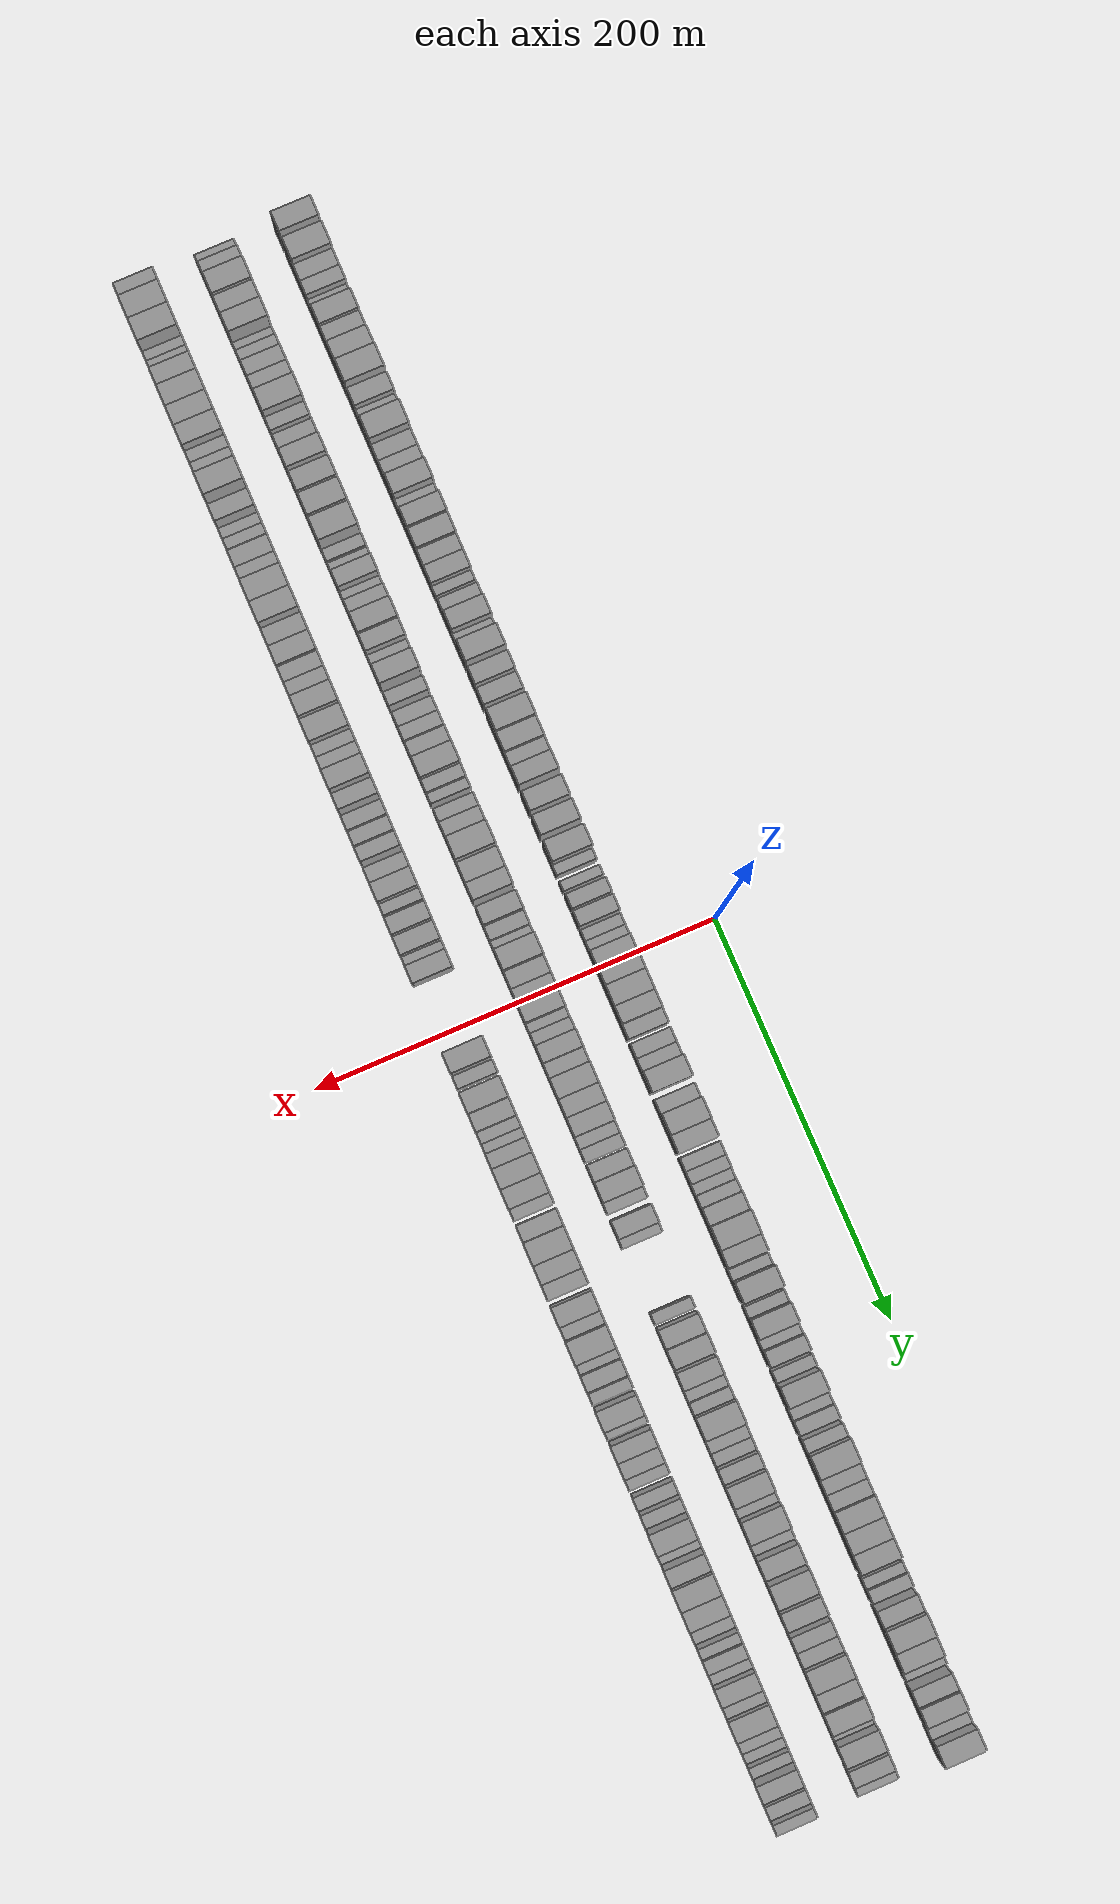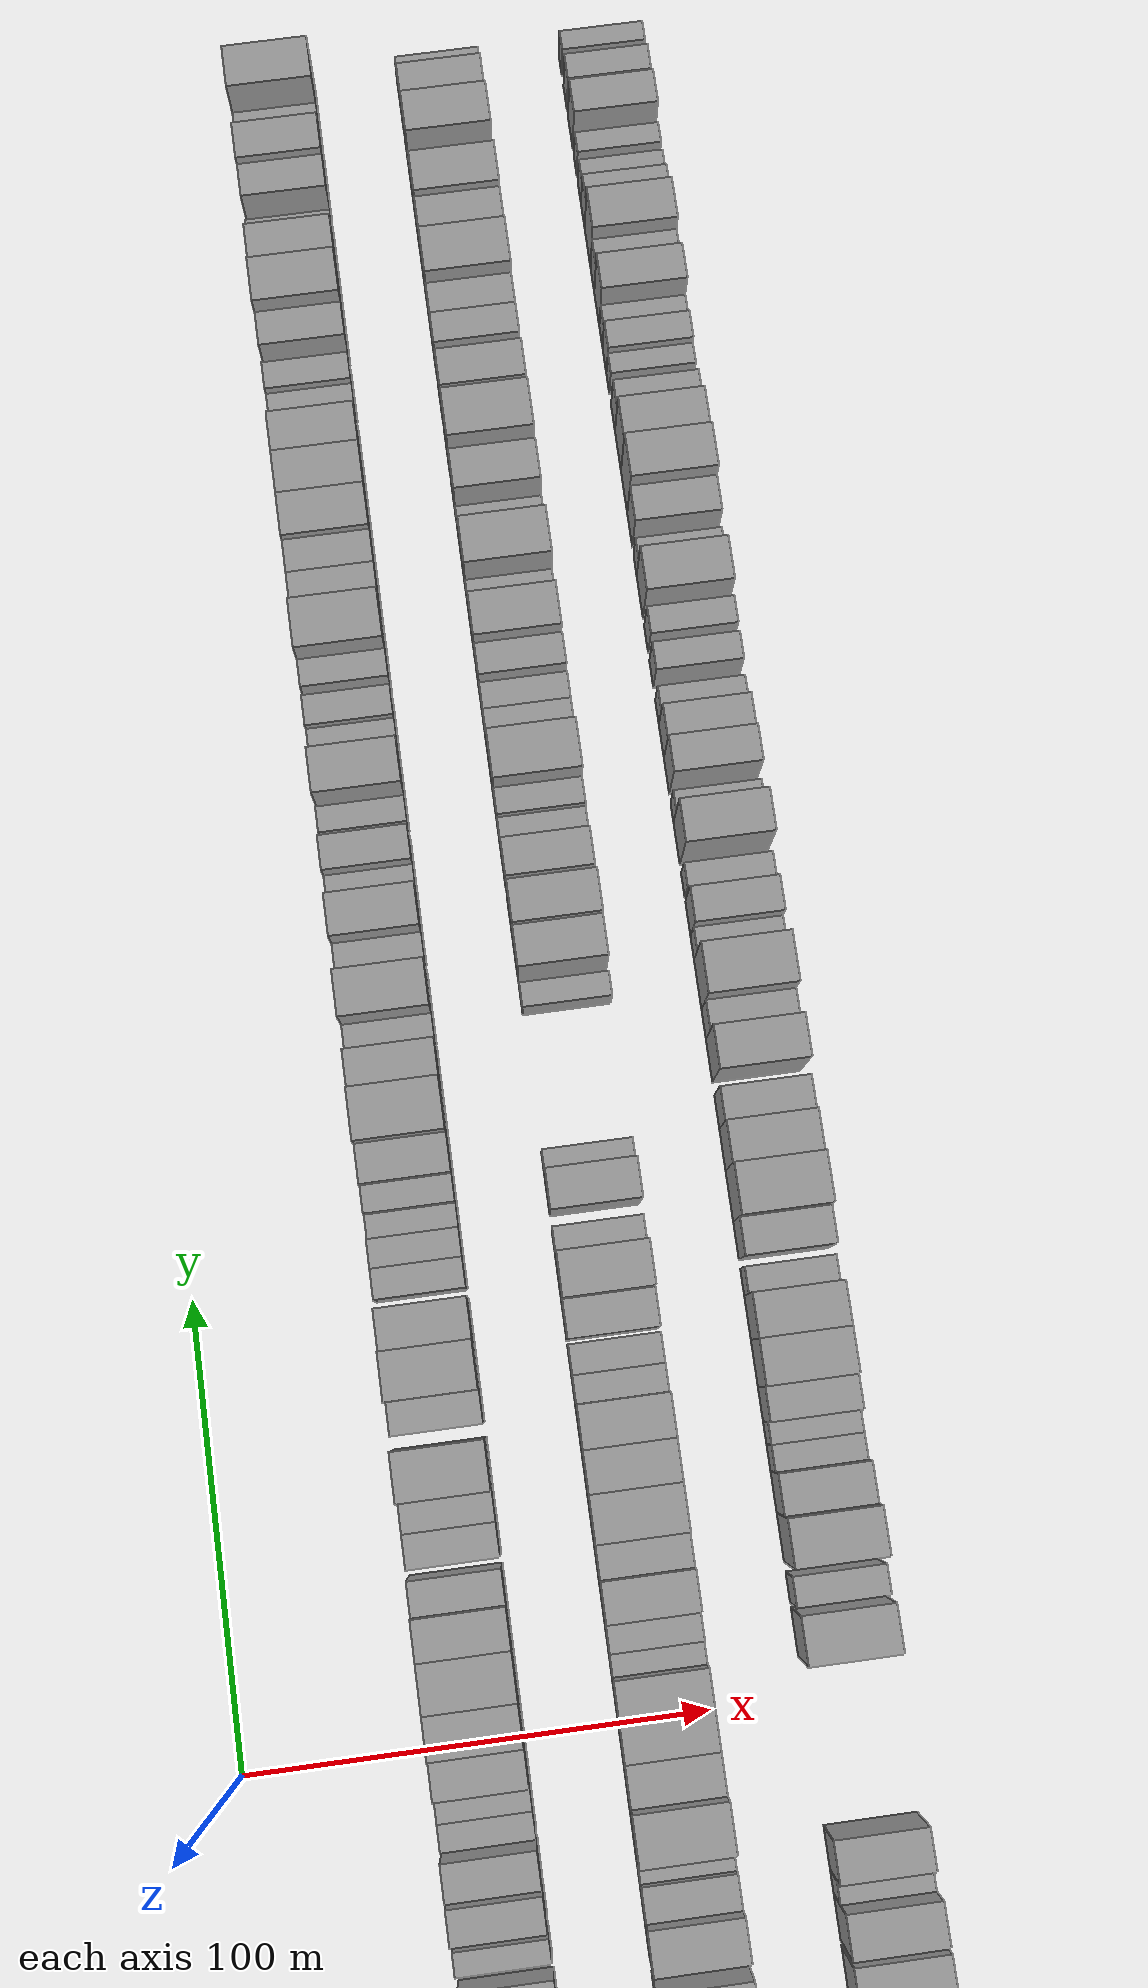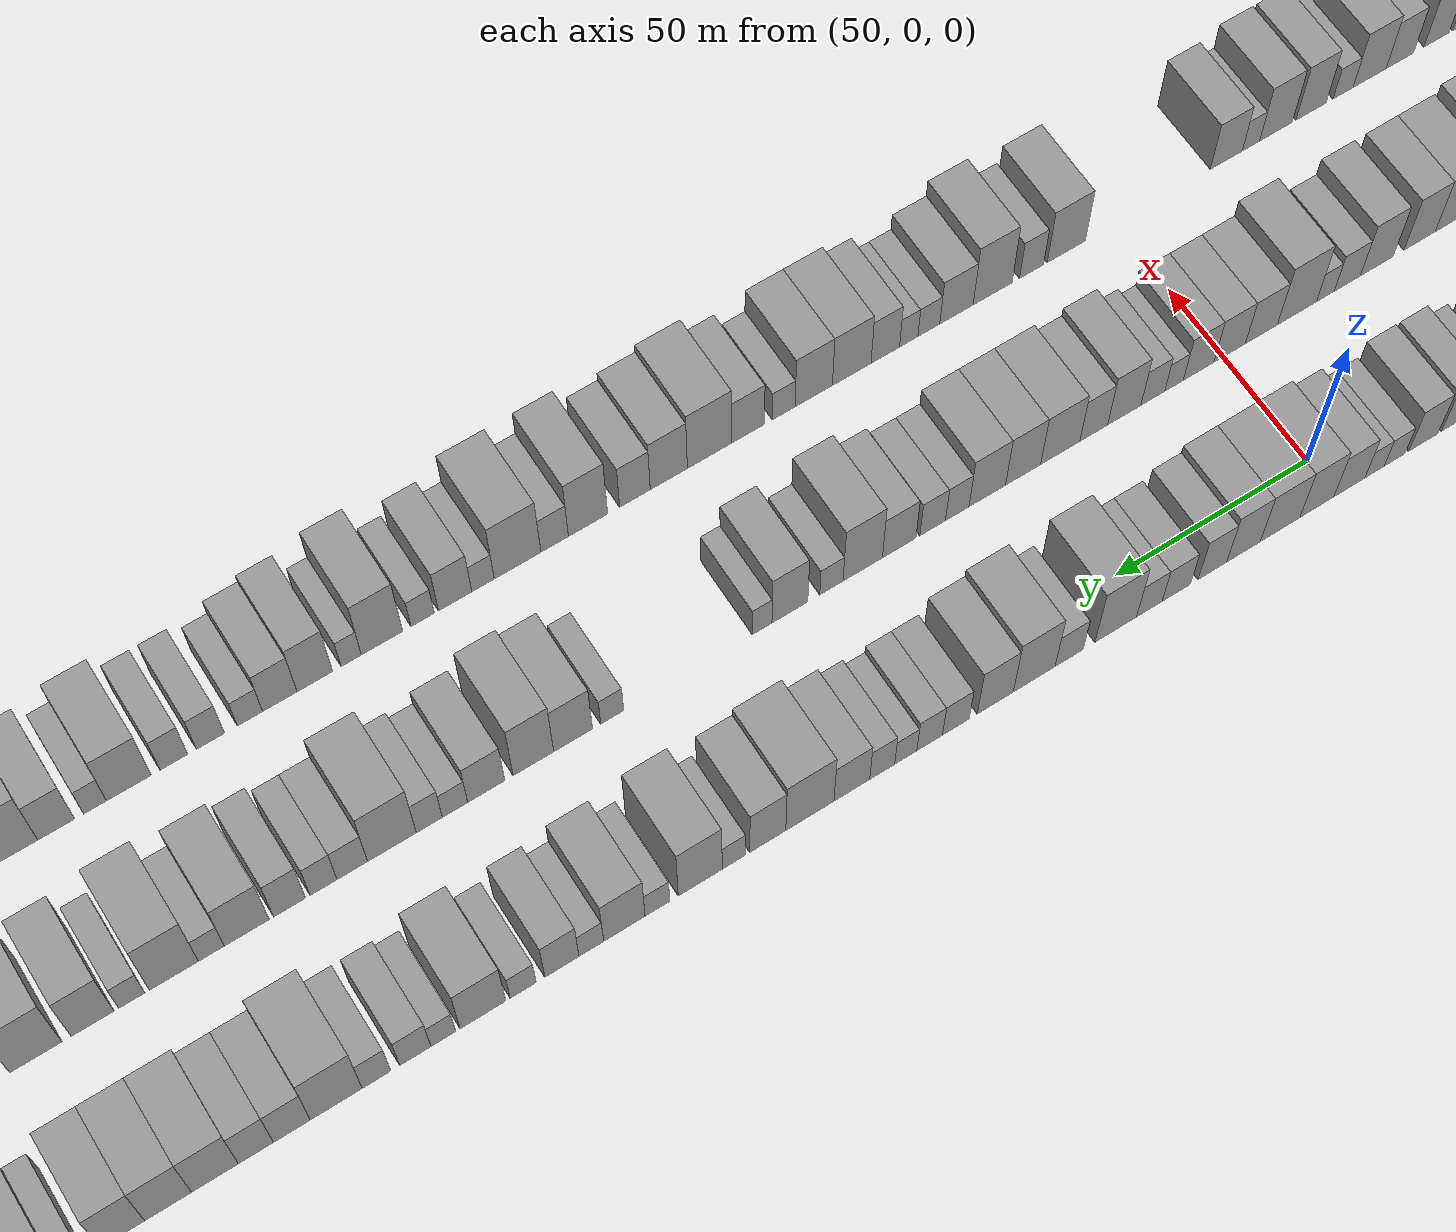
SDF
<sdf version="1.6">
 <world name="default">
  <scene>
   <sky><clouds><speed>12</speed></clouds></sky>
   <ambient>0.4 0.4 0.4 1</ambient>
   <background>0.7 0.7 0.7 1</background>
   <shadows>1</shadows>
  </scene>
  <gravity>0 0 -9.8066</gravity>
  <magnetic_field>6e-06 2.3e-05 -4.2e-05</magnetic_field>
  <physics default="0" name="default_physics" type="ode">
   <ode>
    <solver>
     <type>quick</type>
     <iters>10</iters>
     <sor>1.0</sor>
     <use_dynamic_moi_rescaling>0</use_dynamic_moi_rescaling>
    </solver>
    <constraints>
     <cfm>0</cfm>
     <erp>0.2</erp>
     <contact_max_correcting_vel>100</contact_max_correcting_vel>
     <contact_surface_layer>0.001</contact_surface_layer>
    </constraints>
   </ode>
   <max_step_size>0.004</max_step_size>
   <real_time_factor>1</real_time_factor>
   <real_time_update_rate>250</real_time_update_rate>
  </physics>
  <light name="sun" type="directional">
   <pose>0 0 10 0 0 0</pose>
   <diffuse>0.8 0.8 0.8 1</diffuse>
   <specular>0.2 0.2 0.2 1</specular>
   <attenuation>
    <range>1000</range>
    <constant>0.9</constant>
    <linear>0.01</linear>
    <quadratic>0.001</quadratic>
   </attenuation>
   <direction>-0.5 0.1 -0.9</direction>
  </light>
  <model name="building_1">
   <static>1</static>
   <pose>50.0000 -374.9445 0 0.000000 0.000000 0.000000</pose>
   <link name="link">
    <pose>0 0 12.00 0 0 0</pose>
    <collision name="collision"><geometry><box><size>20.0000 10.1110 24.0000</size></box></geometry></collision>
    <visual name="visual">
     <cast_shadows>0</cast_shadows>
     <geometry><box><size>20.0000 10.1110 24.0000</size></box></geometry>
     <material>
      <script>
       <uri>model://grey_wall/materials/scripts</uri>
       <uri>model://grey_wall/materials/textures</uri>
       <name>vrc/grey_wall</name>
      </script>
     </material>
    </visual>
   </link>
  </model>
  <model name="building_2">
   <static>1</static>
   <pose>50.0000 -361.0823 0 0.000000 0.000000 0.000000</pose>
   <link name="link">
    <pose>0 0 12.00 0 0 0</pose>
    <collision name="collision"><geometry><box><size>20.0000 11.6134 24.0000</size></box></geometry></collision>
    <visual name="visual">
     <cast_shadows>0</cast_shadows>
     <geometry><box><size>20.0000 11.6134 24.0000</size></box></geometry>
     <material>
      <script>
       <uri>model://grey_wall/materials/scripts</uri>
       <uri>model://grey_wall/materials/textures</uri>
       <name>vrc/grey_wall</name>
      </script>
     </material>
    </visual>
   </link>
  </model>
  <model name="building_3">
   <static>1</static>
   <pose>50.0000 -351.0350 0 0.000000 0.000000 0.000000</pose>
   <link name="link">
    <pose>0 0 9.00 0 0 0</pose>
    <collision name="collision"><geometry><box><size>20.0000 8.4814 18.0000</size></box></geometry></collision>
    <visual name="visual">
     <cast_shadows>0</cast_shadows>
     <geometry><box><size>20.0000 8.4814 18.0000</size></box></geometry>
     <material>
      <script>
       <uri>model://grey_wall/materials/scripts</uri>
       <uri>model://grey_wall/materials/textures</uri>
       <name>vrc/grey_wall</name>
      </script>
     </material>
    </visual>
   </link>
  </model>
  <model name="building_4">
   <static>1</static>
   <pose>50.0000 -343.1112 0 0.000000 0.000000 0.000000</pose>
   <link name="link">
    <pose>0 0 9.00 0 0 0</pose>
    <collision name="collision"><geometry><box><size>20.0000 7.3661 18.0000</size></box></geometry></collision>
    <visual name="visual">
     <cast_shadows>0</cast_shadows>
     <geometry><box><size>20.0000 7.3661 18.0000</size></box></geometry>
     <material>
      <script>
       <uri>model://grey_wall/materials/scripts</uri>
       <uri>model://grey_wall/materials/textures</uri>
       <name>vrc/grey_wall</name>
      </script>
     </material>
    </visual>
   </link>
  </model>
  <model name="building_5">
   <static>1</static>
   <pose>50.0000 -336.4441 0 0.000000 0.000000 0.000000</pose>
   <link name="link">
    <pose>0 0 6.00 0 0 0</pose>
    <collision name="collision"><geometry><box><size>20.0000 5.9682 12.0000</size></box></geometry></collision>
    <visual name="visual">
     <cast_shadows>0</cast_shadows>
     <geometry><box><size>20.0000 5.9682 12.0000</size></box></geometry>
     <material>
      <script>
       <uri>model://grey_wall/materials/scripts</uri>
       <uri>model://grey_wall/materials/textures</uri>
       <name>vrc/grey_wall</name>
      </script>
     </material>
    </visual>
   </link>
  </model>
  <model name="building_6">
   <static>1</static>
   <pose>50.0000 -328.4006 0 0.000000 0.000000 0.000000</pose>
   <link name="link">
    <pose>0 0 10.50 0 0 0</pose>
    <collision name="collision"><geometry><box><size>20.0000 10.1188 21.0000</size></box></geometry></collision>
    <visual name="visual">
     <cast_shadows>0</cast_shadows>
     <geometry><box><size>20.0000 10.1188 21.0000</size></box></geometry>
     <material>
      <script>
       <uri>model://grey_wall/materials/scripts</uri>
       <uri>model://grey_wall/materials/textures</uri>
       <name>vrc/grey_wall</name>
      </script>
     </material>
    </visual>
   </link>
  </model>
  <model name="building_7">
   <static>1</static>
   <pose>50.0000 -319.0140 0 0.000000 0.000000 0.000000</pose>
   <link name="link">
    <pose>0 0 9.00 0 0 0</pose>
    <collision name="collision"><geometry><box><size>20.0000 8.6544 18.0000</size></box></geometry></collision>
    <visual name="visual">
     <cast_shadows>0</cast_shadows>
     <geometry><box><size>20.0000 8.6544 18.0000</size></box></geometry>
     <material>
      <script>
       <uri>model://grey_wall/materials/scripts</uri>
       <uri>model://grey_wall/materials/textures</uri>
       <name>vrc/grey_wall</name>
      </script>
     </material>
    </visual>
   </link>
  </model>
  <model name="building_8">
   <static>1</static>
   <pose>50.0000 -309.4827 0 0.000000 0.000000 0.000000</pose>
   <link name="link">
    <pose>0 0 10.50 0 0 0</pose>
    <collision name="collision"><geometry><box><size>20.0000 10.4083 21.0000</size></box></geometry></collision>
    <visual name="visual">
     <cast_shadows>0</cast_shadows>
     <geometry><box><size>20.0000 10.4083 21.0000</size></box></geometry>
     <material>
      <script>
       <uri>model://grey_wall/materials/scripts</uri>
       <uri>model://grey_wall/materials/textures</uri>
       <name>vrc/grey_wall</name>
      </script>
     </material>
    </visual>
   </link>
  </model>
  <model name="building_9">
   <static>1</static>
   <pose>50.0000 -298.4291 0 0.000000 0.000000 0.000000</pose>
   <link name="link">
    <pose>0 0 12.00 0 0 0</pose>
    <collision name="collision"><geometry><box><size>20.0000 11.6989 24.0000</size></box></geometry></collision>
    <visual name="visual">
     <cast_shadows>0</cast_shadows>
     <geometry><box><size>20.0000 11.6989 24.0000</size></box></geometry>
     <material>
      <script>
       <uri>model://grey_wall/materials/scripts</uri>
       <uri>model://grey_wall/materials/textures</uri>
       <name>vrc/grey_wall</name>
      </script>
     </material>
    </visual>
   </link>
  </model>
  <model name="building_10">
   <static>1</static>
   <pose>50.0000 -286.0297 0 0.000000 0.000000 0.000000</pose>
   <link name="link">
    <pose>0 0 10.50 0 0 0</pose>
    <collision name="collision"><geometry><box><size>20.0000 9.0999 21.0000</size></box></geometry></collision>
    <visual name="visual">
     <cast_shadows>0</cast_shadows>
     <geometry><box><size>20.0000 9.0999 21.0000</size></box></geometry>
     <material>
      <script>
       <uri>model://grey_wall/materials/scripts</uri>
       <uri>model://grey_wall/materials/textures</uri>
       <name>vrc/grey_wall</name>
      </script>
     </material>
    </visual>
   </link>
  </model>
  <model name="building_11">
   <static>1</static>
   <pose>50.0000 -278.4642 0 0.000000 0.000000 0.000000</pose>
   <link name="link">
    <pose>0 0 7.50 0 0 0</pose>
    <collision name="collision"><geometry><box><size>20.0000 6.0311 15.0000</size></box></geometry></collision>
    <visual name="visual">
     <cast_shadows>0</cast_shadows>
     <geometry><box><size>20.0000 6.0311 15.0000</size></box></geometry>
     <material>
      <script>
       <uri>model://grey_wall/materials/scripts</uri>
       <uri>model://grey_wall/materials/textures</uri>
       <name>vrc/grey_wall</name>
      </script>
     </material>
    </visual>
   </link>
  </model>
  <model name="building_12">
   <static>1</static>
   <pose>50.0000 -269.5073 0 0.000000 0.000000 0.000000</pose>
   <link name="link">
    <pose>0 0 12.00 0 0 0</pose>
    <collision name="collision"><geometry><box><size>20.0000 11.8829 24.0000</size></box></geometry></collision>
    <visual name="visual">
     <cast_shadows>0</cast_shadows>
     <geometry><box><size>20.0000 11.8829 24.0000</size></box></geometry>
     <material>
      <script>
       <uri>model://grey_wall/materials/scripts</uri>
       <uri>model://grey_wall/materials/textures</uri>
       <name>vrc/grey_wall</name>
      </script>
     </material>
    </visual>
   </link>
  </model>
  <model name="building_13">
   <static>1</static>
   <pose>50.0000 -258.4388 0 0.000000 0.000000 0.000000</pose>
   <link name="link">
    <pose>0 0 9.00 0 0 0</pose>
    <collision name="collision"><geometry><box><size>20.0000 8.2542 18.0000</size></box></geometry></collision>
    <visual name="visual">
     <cast_shadows>0</cast_shadows>
     <geometry><box><size>20.0000 8.2542 18.0000</size></box></geometry>
     <material>
      <script>
       <uri>model://grey_wall/materials/scripts</uri>
       <uri>model://grey_wall/materials/textures</uri>
       <name>vrc/grey_wall</name>
      </script>
     </material>
    </visual>
   </link>
  </model>
  <model name="building_14">
   <static>1</static>
   <pose>50.0000 -250.0580 0 0.000000 0.000000 0.000000</pose>
   <link name="link">
    <pose>0 0 9.00 0 0 0</pose>
    <collision name="collision"><geometry><box><size>20.0000 8.5073 18.0000</size></box></geometry></collision>
    <visual name="visual">
     <cast_shadows>0</cast_shadows>
     <geometry><box><size>20.0000 8.5073 18.0000</size></box></geometry>
     <material>
      <script>
       <uri>model://grey_wall/materials/scripts</uri>
       <uri>model://grey_wall/materials/textures</uri>
       <name>vrc/grey_wall</name>
      </script>
     </material>
    </visual>
   </link>
  </model>
  <model name="building_15">
   <static>1</static>
   <pose>50.0000 -240.6390 0 0.000000 0.000000 0.000000</pose>
   <link name="link">
    <pose>0 0 12.00 0 0 0</pose>
    <collision name="collision"><geometry><box><size>20.0000 10.3308 24.0000</size></box></geometry></collision>
    <visual name="visual">
     <cast_shadows>0</cast_shadows>
     <geometry><box><size>20.0000 10.3308 24.0000</size></box></geometry>
     <material>
      <script>
       <uri>model://grey_wall/materials/scripts</uri>
       <uri>model://grey_wall/materials/textures</uri>
       <name>vrc/grey_wall</name>
      </script>
     </material>
    </visual>
   </link>
  </model>
  <model name="building_16">
   <static>1</static>
   <pose>50.0000 -232.1779 0 0.000000 0.000000 0.000000</pose>
   <link name="link">
    <pose>0 0 7.50 0 0 0</pose>
    <collision name="collision"><geometry><box><size>20.0000 6.5913 15.0000</size></box></geometry></collision>
    <visual name="visual">
     <cast_shadows>0</cast_shadows>
     <geometry><box><size>20.0000 6.5913 15.0000</size></box></geometry>
     <material>
      <script>
       <uri>model://grey_wall/materials/scripts</uri>
       <uri>model://grey_wall/materials/textures</uri>
       <name>vrc/grey_wall</name>
      </script>
     </material>
    </visual>
   </link>
  </model>
  <model name="building_17">
   <static>1</static>
   <pose>50.0000 -224.0062 0 0.000000 0.000000 0.000000</pose>
   <link name="link">
    <pose>0 0 12.00 0 0 0</pose>
    <collision name="collision"><geometry><box><size>20.0000 9.7523 24.0000</size></box></geometry></collision>
    <visual name="visual">
     <cast_shadows>0</cast_shadows>
     <geometry><box><size>20.0000 9.7523 24.0000</size></box></geometry>
     <material>
      <script>
       <uri>model://grey_wall/materials/scripts</uri>
       <uri>model://grey_wall/materials/textures</uri>
       <name>vrc/grey_wall</name>
      </script>
     </material>
    </visual>
   </link>
  </model>
  <model name="building_18">
   <static>1</static>
   <pose>50.0000 -214.1113 0 0.000000 0.000000 0.000000</pose>
   <link name="link">
    <pose>0 0 10.50 0 0 0</pose>
    <collision name="collision"><geometry><box><size>20.0000 10.0374 21.0000</size></box></geometry></collision>
    <visual name="visual">
     <cast_shadows>0</cast_shadows>
     <geometry><box><size>20.0000 10.0374 21.0000</size></box></geometry>
     <material>
      <script>
       <uri>model://grey_wall/materials/scripts</uri>
       <uri>model://grey_wall/materials/textures</uri>
       <name>vrc/grey_wall</name>
      </script>
     </material>
    </visual>
   </link>
  </model>
  <model name="building_19">
   <static>1</static>
   <pose>50.0000 -205.0495 0 0.000000 0.000000 0.000000</pose>
   <link name="link">
    <pose>0 0 9.00 0 0 0</pose>
    <collision name="collision"><geometry><box><size>20.0000 8.0863 18.0000</size></box></geometry></collision>
    <visual name="visual">
     <cast_shadows>0</cast_shadows>
     <geometry><box><size>20.0000 8.0863 18.0000</size></box></geometry>
     <material>
      <script>
       <uri>model://grey_wall/materials/scripts</uri>
       <uri>model://grey_wall/materials/textures</uri>
       <name>vrc/grey_wall</name>
      </script>
     </material>
    </visual>
   </link>
  </model>
  <model name="building_20">
   <static>1</static>
   <pose>50.0000 -196.5198 0 0.000000 0.000000 0.000000</pose>
   <link name="link">
    <pose>0 0 9.00 0 0 0</pose>
    <collision name="collision"><geometry><box><size>20.0000 8.9729 18.0000</size></box></geometry></collision>
    <visual name="visual">
     <cast_shadows>0</cast_shadows>
     <geometry><box><size>20.0000 8.9729 18.0000</size></box></geometry>
     <material>
      <script>
       <uri>model://grey_wall/materials/scripts</uri>
       <uri>model://grey_wall/materials/textures</uri>
       <name>vrc/grey_wall</name>
      </script>
     </material>
    </visual>
   </link>
  </model>
  <model name="building_21">
   <static>1</static>
   <pose>50.0000 -189.4795 0 0.000000 0.000000 0.000000</pose>
   <link name="link">
    <pose>0 0 6.00 0 0 0</pose>
    <collision name="collision"><geometry><box><size>20.0000 5.1077 12.0000</size></box></geometry></collision>
    <visual name="visual">
     <cast_shadows>0</cast_shadows>
     <geometry><box><size>20.0000 5.1077 12.0000</size></box></geometry>
     <material>
      <script>
       <uri>model://grey_wall/materials/scripts</uri>
       <uri>model://grey_wall/materials/textures</uri>
       <name>vrc/grey_wall</name>
      </script>
     </material>
    </visual>
   </link>
  </model>
  <model name="building_22">
   <static>1</static>
   <pose>50.0000 -181.2053 0 0.000000 0.000000 0.000000</pose>
   <link name="link">
    <pose>0 0 7.50 0 0 0</pose>
    <collision name="collision"><geometry><box><size>20.0000 7.4408 15.0000</size></box></geometry></collision>
    <visual name="visual">
     <cast_shadows>0</cast_shadows>
     <geometry><box><size>20.0000 7.4408 15.0000</size></box></geometry>
     <material>
      <script>
       <uri>model://grey_wall/materials/scripts</uri>
       <uri>model://grey_wall/materials/textures</uri>
       <name>vrc/grey_wall</name>
      </script>
     </material>
    </visual>
   </link>
  </model>
  <model name="building_23">
   <static>1</static>
   <pose>50.0000 -172.6425 0 0.000000 0.000000 0.000000</pose>
   <link name="link">
    <pose>0 0 10.50 0 0 0</pose>
    <collision name="collision"><geometry><box><size>20.0000 9.6848 21.0000</size></box></geometry></collision>
    <visual name="visual">
     <cast_shadows>0</cast_shadows>
     <geometry><box><size>20.0000 9.6848 21.0000</size></box></geometry>
     <material>
      <script>
       <uri>model://grey_wall/materials/scripts</uri>
       <uri>model://grey_wall/materials/textures</uri>
       <name>vrc/grey_wall</name>
      </script>
     </material>
    </visual>
   </link>
  </model>
  <model name="building_24">
   <static>1</static>
   <pose>50.0000 -164.8970 0 0.000000 0.000000 0.000000</pose>
   <link name="link">
    <pose>0 0 6.00 0 0 0</pose>
    <collision name="collision"><geometry><box><size>20.0000 5.8061 12.0000</size></box></geometry></collision>
    <visual name="visual">
     <cast_shadows>0</cast_shadows>
     <geometry><box><size>20.0000 5.8061 12.0000</size></box></geometry>
     <material>
      <script>
       <uri>model://grey_wall/materials/scripts</uri>
       <uri>model://grey_wall/materials/textures</uri>
       <name>vrc/grey_wall</name>
      </script>
     </material>
    </visual>
   </link>
  </model>
  <model name="building_25">
   <static>1</static>
   <pose>50.0000 -156.5875 0 0.000000 0.000000 0.000000</pose>
   <link name="link">
    <pose>0 0 12.00 0 0 0</pose>
    <collision name="collision"><geometry><box><size>20.0000 10.8130 24.0000</size></box></geometry></collision>
    <visual name="visual">
     <cast_shadows>0</cast_shadows>
     <geometry><box><size>20.0000 10.8130 24.0000</size></box></geometry>
     <material>
      <script>
       <uri>model://grey_wall/materials/scripts</uri>
       <uri>model://grey_wall/materials/textures</uri>
       <name>vrc/grey_wall</name>
      </script>
     </material>
    </visual>
   </link>
  </model>
  <model name="building_26">
   <static>1</static>
   <pose>50.0000 -144.6753 0 0.000000 0.000000 0.000000</pose>
   <link name="link">
    <pose>0 0 10.50 0 0 0</pose>
    <collision name="collision"><geometry><box><size>20.0000 9.0112 21.0000</size></box></geometry></collision>
    <visual name="visual">
     <cast_shadows>0</cast_shadows>
     <geometry><box><size>20.0000 9.0112 21.0000</size></box></geometry>
     <material>
      <script>
       <uri>model://grey_wall/materials/scripts</uri>
       <uri>model://grey_wall/materials/textures</uri>
       <name>vrc/grey_wall</name>
      </script>
     </material>
    </visual>
   </link>
  </model>
  <model name="building_27">
   <static>1</static>
   <pose>50.0000 -134.8729 0 0.000000 0.000000 0.000000</pose>
   <link name="link">
    <pose>0 0 9.00 0 0 0</pose>
    <collision name="collision"><geometry><box><size>20.0000 8.5936 18.0000</size></box></geometry></collision>
    <visual name="visual">
     <cast_shadows>0</cast_shadows>
     <geometry><box><size>20.0000 8.5936 18.0000</size></box></geometry>
     <material>
      <script>
       <uri>model://grey_wall/materials/scripts</uri>
       <uri>model://grey_wall/materials/textures</uri>
       <name>vrc/grey_wall</name>
      </script>
     </material>
    </visual>
   </link>
  </model>
  <model name="building_28">
   <static>1</static>
   <pose>50.0000 -121.9977 0 0.000000 0.000000 0.000000</pose>
   <link name="link">
    <pose>0 0 12.00 0 0 0</pose>
    <collision name="collision"><geometry><box><size>20.0000 11.1568 24.0000</size></box></geometry></collision>
    <visual name="visual">
     <cast_shadows>0</cast_shadows>
     <geometry><box><size>20.0000 11.1568 24.0000</size></box></geometry>
     <material>
      <script>
       <uri>model://grey_wall/materials/scripts</uri>
       <uri>model://grey_wall/materials/textures</uri>
       <name>vrc/grey_wall</name>
      </script>
     </material>
    </visual>
   </link>
  </model>
  <model name="building_29">
   <static>1</static>
   <pose>50.0000 -111.4554 0 0.000000 0.000000 0.000000</pose>
   <link name="link">
    <pose>0 0 10.50 0 0 0</pose>
    <collision name="collision"><geometry><box><size>20.0000 9.9280 21.0000</size></box></geometry></collision>
    <visual name="visual">
     <cast_shadows>0</cast_shadows>
     <geometry><box><size>20.0000 9.9280 21.0000</size></box></geometry>
     <material>
      <script>
       <uri>model://grey_wall/materials/scripts</uri>
       <uri>model://grey_wall/materials/textures</uri>
       <name>vrc/grey_wall</name>
      </script>
     </material>
    </visual>
   </link>
  </model>
  <model name="building_30">
   <static>1</static>
   <pose>50.0000 -102.8536 0 0.000000 0.000000 0.000000</pose>
   <link name="link">
    <pose>0 0 9.00 0 0 0</pose>
    <collision name="collision"><geometry><box><size>20.0000 7.2755 18.0000</size></box></geometry></collision>
    <visual name="visual">
     <cast_shadows>0</cast_shadows>
     <geometry><box><size>20.0000 7.2755 18.0000</size></box></geometry>
     <material>
      <script>
       <uri>model://grey_wall/materials/scripts</uri>
       <uri>model://grey_wall/materials/textures</uri>
       <name>vrc/grey_wall</name>
      </script>
     </material>
    </visual>
   </link>
  </model>
  <model name="building_31">
   <static>1</static>
   <pose>50.0000 -94.5185 0 0.000000 0.000000 0.000000</pose>
   <link name="link">
    <pose>0 0 10.50 0 0 0</pose>
    <collision name="collision"><geometry><box><size>20.0000 9.3947 21.0000</size></box></geometry></collision>
    <visual name="visual">
     <cast_shadows>0</cast_shadows>
     <geometry><box><size>20.0000 9.3947 21.0000</size></box></geometry>
     <material>
      <script>
       <uri>model://grey_wall/materials/scripts</uri>
       <uri>model://grey_wall/materials/textures</uri>
       <name>vrc/grey_wall</name>
      </script>
     </material>
    </visual>
   </link>
  </model>
  <model name="building_32">
   <static>1</static>
   <pose>50.0000 -81.8265 0 0.000000 0.000000 0.000000</pose>
   <link name="link">
    <pose>0 0 10.50 0 0 0</pose>
    <collision name="collision"><geometry><box><size>20.0000 9.9894 21.0000</size></box></geometry></collision>
    <visual name="visual">
     <cast_shadows>0</cast_shadows>
     <geometry><box><size>20.0000 9.9894 21.0000</size></box></geometry>
     <material>
      <script>
       <uri>model://grey_wall/materials/scripts</uri>
       <uri>model://grey_wall/materials/textures</uri>
       <name>vrc/grey_wall</name>
      </script>
     </material>
    </visual>
   </link>
  </model>
  <model name="building_33">
   <static>1</static>
   <pose>50.0000 -69.7775 0 0.000000 0.000000 0.000000</pose>
   <link name="link">
    <pose>0 0 10.50 0 0 0</pose>
    <collision name="collision"><geometry><box><size>20.0000 10.1087 21.0000</size></box></geometry></collision>
    <visual name="visual">
     <cast_shadows>0</cast_shadows>
     <geometry><box><size>20.0000 10.1087 21.0000</size></box></geometry>
     <material>
      <script>
       <uri>model://grey_wall/materials/scripts</uri>
       <uri>model://grey_wall/materials/textures</uri>
       <name>vrc/grey_wall</name>
      </script>
     </material>
    </visual>
   </link>
  </model>
  <model name="building_34">
   <static>1</static>
   <pose>50.0000 -56.4884 0 0.000000 0.000000 0.000000</pose>
   <link name="link">
    <pose>0 0 12.00 0 0 0</pose>
    <collision name="collision"><geometry><box><size>20.0000 10.4695 24.0000</size></box></geometry></collision>
    <visual name="visual">
     <cast_shadows>0</cast_shadows>
     <geometry><box><size>20.0000 10.4695 24.0000</size></box></geometry>
     <material>
      <script>
       <uri>model://grey_wall/materials/scripts</uri>
       <uri>model://grey_wall/materials/textures</uri>
       <name>vrc/grey_wall</name>
      </script>
     </material>
    </visual>
   </link>
  </model>
  <model name="building_35">
   <static>1</static>
   <pose>50.0000 -48.6199 0 0.000000 0.000000 0.000000</pose>
   <link name="link">
    <pose>0 0 6.00 0 0 0</pose>
    <collision name="collision"><geometry><box><size>20.0000 5.2676 12.0000</size></box></geometry></collision>
    <visual name="visual">
     <cast_shadows>0</cast_shadows>
     <geometry><box><size>20.0000 5.2676 12.0000</size></box></geometry>
     <material>
      <script>
       <uri>model://grey_wall/materials/scripts</uri>
       <uri>model://grey_wall/materials/textures</uri>
       <name>vrc/grey_wall</name>
      </script>
     </material>
    </visual>
   </link>
  </model>
  <model name="building_36">
   <static>1</static>
   <pose>50.0000 -40.5141 0 0.000000 0.000000 0.000000</pose>
   <link name="link">
    <pose>0 0 6.00 0 0 0</pose>
    <collision name="collision"><geometry><box><size>20.0000 4.9439 12.0000</size></box></geometry></collision>
    <visual name="visual">
     <cast_shadows>0</cast_shadows>
     <geometry><box><size>20.0000 4.9439 12.0000</size></box></geometry>
     <material>
      <script>
       <uri>model://grey_wall/materials/scripts</uri>
       <uri>model://grey_wall/materials/textures</uri>
       <name>vrc/grey_wall</name>
      </script>
     </material>
    </visual>
   </link>
  </model>
  <model name="building_37">
   <static>1</static>
   <pose>50.0000 -32.3380 0 0.000000 0.000000 0.000000</pose>
   <link name="link">
    <pose>0 0 9.00 0 0 0</pose>
    <collision name="collision"><geometry><box><size>20.0000 7.4083 18.0000</size></box></geometry></collision>
    <visual name="visual">
     <cast_shadows>0</cast_shadows>
     <geometry><box><size>20.0000 7.4083 18.0000</size></box></geometry>
     <material>
      <script>
       <uri>model://grey_wall/materials/scripts</uri>
       <uri>model://grey_wall/materials/textures</uri>
       <name>vrc/grey_wall</name>
      </script>
     </material>
    </visual>
   </link>
  </model>
  <model name="building_38">
   <static>1</static>
   <pose>50.0000 -23.7033 0 0.000000 0.000000 0.000000</pose>
   <link name="link">
    <pose>0 0 9.00 0 0 0</pose>
    <collision name="collision"><geometry><box><size>20.0000 7.8612 18.0000</size></box></geometry></collision>
    <visual name="visual">
     <cast_shadows>0</cast_shadows>
     <geometry><box><size>20.0000 7.8612 18.0000</size></box></geometry>
     <material>
      <script>
       <uri>model://grey_wall/materials/scripts</uri>
       <uri>model://grey_wall/materials/textures</uri>
       <name>vrc/grey_wall</name>
      </script>
     </material>
    </visual>
   </link>
  </model>
  <model name="building_39">
   <static>1</static>
   <pose>50.0000 -15.9602 0 0.000000 0.000000 0.000000</pose>
   <link name="link">
    <pose>0 0 6.00 0 0 0</pose>
    <collision name="collision"><geometry><box><size>20.0000 5.6249 12.0000</size></box></geometry></collision>
    <visual name="visual">
     <cast_shadows>0</cast_shadows>
     <geometry><box><size>20.0000 5.6249 12.0000</size></box></geometry>
     <material>
      <script>
       <uri>model://grey_wall/materials/scripts</uri>
       <uri>model://grey_wall/materials/textures</uri>
       <name>vrc/grey_wall</name>
      </script>
     </material>
    </visual>
   </link>
  </model>
  <model name="building_40">
   <static>1</static>
   <pose>50.0000 -10.5560 0 0.000000 0.000000 0.000000</pose>
   <link name="link">
    <pose>0 0 6.00 0 0 0</pose>
    <collision name="collision"><geometry><box><size>20.0000 5.1836 12.0000</size></box></geometry></collision>
    <visual name="visual">
     <cast_shadows>0</cast_shadows>
     <geometry><box><size>20.0000 5.1836 12.0000</size></box></geometry>
     <material>
      <script>
       <uri>model://grey_wall/materials/scripts</uri>
       <uri>model://grey_wall/materials/textures</uri>
       <name>vrc/grey_wall</name>
      </script>
     </material>
    </visual>
   </link>
  </model>
  <model name="building_41">
   <static>1</static>
   <pose>50.0000 -3.8160 0 0.000000 0.000000 0.000000</pose>
   <link name="link">
    <pose>0 0 9.00 0 0 0</pose>
    <collision name="collision"><geometry><box><size>20.0000 8.2964 18.0000</size></box></geometry></collision>
    <visual name="visual">
     <cast_shadows>0</cast_shadows>
     <geometry><box><size>20.0000 8.2964 18.0000</size></box></geometry>
     <material>
      <script>
       <uri>model://grey_wall/materials/scripts</uri>
       <uri>model://grey_wall/materials/textures</uri>
       <name>vrc/grey_wall</name>
      </script>
     </material>
    </visual>
   </link>
  </model>
  <model name="building_42">
   <static>1</static>
   <pose>50.0000 4.8499 0 0.000000 0.000000 0.000000</pose>
   <link name="link">
    <pose>0 0 10.50 0 0 0</pose>
    <collision name="collision"><geometry><box><size>20.0000 9.0354 21.0000</size></box></geometry></collision>
    <visual name="visual">
     <cast_shadows>0</cast_shadows>
     <geometry><box><size>20.0000 9.0354 21.0000</size></box></geometry>
     <material>
      <script>
       <uri>model://grey_wall/materials/scripts</uri>
       <uri>model://grey_wall/materials/textures</uri>
       <name>vrc/grey_wall</name>
      </script>
     </material>
    </visual>
   </link>
  </model>
  <model name="building_43">
   <static>1</static>
   <pose>50.0000 14.5789 0 0.000000 0.000000 0.000000</pose>
   <link name="link">
    <pose>0 0 10.50 0 0 0</pose>
    <collision name="collision"><geometry><box><size>20.0000 10.4227 21.0000</size></box></geometry></collision>
    <visual name="visual">
     <cast_shadows>0</cast_shadows>
     <geometry><box><size>20.0000 10.4227 21.0000</size></box></geometry>
     <material>
      <script>
       <uri>model://grey_wall/materials/scripts</uri>
       <uri>model://grey_wall/materials/textures</uri>
       <name>vrc/grey_wall</name>
      </script>
     </material>
    </visual>
   </link>
  </model>
  <model name="building_44">
   <static>1</static>
   <pose>50.0000 24.2047 0 0.000000 0.000000 0.000000</pose>
   <link name="link">
    <pose>0 0 10.50 0 0 0</pose>
    <collision name="collision"><geometry><box><size>20.0000 8.8288 21.0000</size></box></geometry></collision>
    <visual name="visual">
     <cast_shadows>0</cast_shadows>
     <geometry><box><size>20.0000 8.8288 21.0000</size></box></geometry>
     <material>
      <script>
       <uri>model://grey_wall/materials/scripts</uri>
       <uri>model://grey_wall/materials/textures</uri>
       <name>vrc/grey_wall</name>
      </script>
     </material>
    </visual>
   </link>
  </model>
  <model name="building_45">
   <static>1</static>
   <pose>50.0000 32.3401 0 0.000000 0.000000 0.000000</pose>
   <link name="link">
    <pose>0 0 9.00 0 0 0</pose>
    <collision name="collision"><geometry><box><size>20.0000 7.4420 18.0000</size></box></geometry></collision>
    <visual name="visual">
     <cast_shadows>0</cast_shadows>
     <geometry><box><size>20.0000 7.4420 18.0000</size></box></geometry>
     <material>
      <script>
       <uri>model://grey_wall/materials/scripts</uri>
       <uri>model://grey_wall/materials/textures</uri>
       <name>vrc/grey_wall</name>
      </script>
     </material>
    </visual>
   </link>
  </model>
  <model name="building_46">
   <static>1</static>
   <pose>50.0000 41.7242 0 0.000000 0.000000 0.000000</pose>
   <link name="link">
    <pose>0 0 7.50 0 0 0</pose>
    <collision name="collision"><geometry><box><size>20.0000 7.3263 15.0000</size></box></geometry></collision>
    <visual name="visual">
     <cast_shadows>0</cast_shadows>
     <geometry><box><size>20.0000 7.3263 15.0000</size></box></geometry>
     <material>
      <script>
       <uri>model://grey_wall/materials/scripts</uri>
       <uri>model://grey_wall/materials/textures</uri>
       <name>vrc/grey_wall</name>
      </script>
     </material>
    </visual>
   </link>
  </model>
  <model name="building_47">
   <static>1</static>
   <pose>50.0000 48.6905 0 0.000000 0.000000 0.000000</pose>
   <link name="link">
    <pose>0 0 7.50 0 0 0</pose>
    <collision name="collision"><geometry><box><size>20.0000 6.6062 15.0000</size></box></geometry></collision>
    <visual name="visual">
     <cast_shadows>0</cast_shadows>
     <geometry><box><size>20.0000 6.6062 15.0000</size></box></geometry>
     <material>
      <script>
       <uri>model://grey_wall/materials/scripts</uri>
       <uri>model://grey_wall/materials/textures</uri>
       <name>vrc/grey_wall</name>
      </script>
     </material>
    </visual>
   </link>
  </model>
  <model name="building_48">
   <static>1</static>
   <pose>50.0000 57.3167 0 0.000000 0.000000 0.000000</pose>
   <link name="link">
    <pose>0 0 12.00 0 0 0</pose>
    <collision name="collision"><geometry><box><size>20.0000 10.6461 24.0000</size></box></geometry></collision>
    <visual name="visual">
     <cast_shadows>0</cast_shadows>
     <geometry><box><size>20.0000 10.6461 24.0000</size></box></geometry>
     <material>
      <script>
       <uri>model://grey_wall/materials/scripts</uri>
       <uri>model://grey_wall/materials/textures</uri>
       <name>vrc/grey_wall</name>
      </script>
     </material>
    </visual>
   </link>
  </model>
  <model name="building_49">
   <static>1</static>
   <pose>50.0000 69.2157 0 0.000000 0.000000 0.000000</pose>
   <link name="link">
    <pose>0 0 7.50 0 0 0</pose>
    <collision name="collision"><geometry><box><size>20.0000 7.1519 15.0000</size></box></geometry></collision>
    <visual name="visual">
     <cast_shadows>0</cast_shadows>
     <geometry><box><size>20.0000 7.1519 15.0000</size></box></geometry>
     <material>
      <script>
       <uri>model://grey_wall/materials/scripts</uri>
       <uri>model://grey_wall/materials/textures</uri>
       <name>vrc/grey_wall</name>
      </script>
     </material>
    </visual>
   </link>
  </model>
  <model name="building_50">
   <static>1</static>
   <pose>50.0000 78.0543 0 0.000000 0.000000 0.000000</pose>
   <link name="link">
    <pose>0 0 12.00 0 0 0</pose>
    <collision name="collision"><geometry><box><size>20.0000 10.5252 24.0000</size></box></geometry></collision>
    <visual name="visual">
     <cast_shadows>0</cast_shadows>
     <geometry><box><size>20.0000 10.5252 24.0000</size></box></geometry>
     <material>
      <script>
       <uri>model://grey_wall/materials/scripts</uri>
       <uri>model://grey_wall/materials/textures</uri>
       <name>vrc/grey_wall</name>
      </script>
     </material>
    </visual>
   </link>
  </model>
  <model name="building_51">
   <static>1</static>
   <pose>50.0000 87.8354 0 0.000000 0.000000 0.000000</pose>
   <link name="link">
    <pose>0 0 10.50 0 0 0</pose>
    <collision name="collision"><geometry><box><size>20.0000 9.0369 21.0000</size></box></geometry></collision>
    <visual name="visual">
     <cast_shadows>0</cast_shadows>
     <geometry><box><size>20.0000 9.0369 21.0000</size></box></geometry>
     <material>
      <script>
       <uri>model://grey_wall/materials/scripts</uri>
       <uri>model://grey_wall/materials/textures</uri>
       <name>vrc/grey_wall</name>
      </script>
     </material>
    </visual>
   </link>
  </model>
  <model name="building_52">
   <static>1</static>
   <pose>50.0000 97.6901 0 0.000000 0.000000 0.000000</pose>
   <link name="link">
    <pose>0 0 7.50 0 0 0</pose>
    <collision name="collision"><geometry><box><size>20.0000 6.6724 15.0000</size></box></geometry></collision>
    <visual name="visual">
     <cast_shadows>0</cast_shadows>
     <geometry><box><size>20.0000 6.6724 15.0000</size></box></geometry>
     <material>
      <script>
       <uri>model://grey_wall/materials/scripts</uri>
       <uri>model://grey_wall/materials/textures</uri>
       <name>vrc/grey_wall</name>
      </script>
     </material>
    </visual>
   </link>
  </model>
  <model name="building_53">
   <static>1</static>
   <pose>50.0000 104.1955 0 0.000000 0.000000 0.000000</pose>
   <link name="link">
    <pose>0 0 7.50 0 0 0</pose>
    <collision name="collision"><geometry><box><size>20.0000 6.3385 15.0000</size></box></geometry></collision>
    <visual name="visual">
     <cast_shadows>0</cast_shadows>
     <geometry><box><size>20.0000 6.3385 15.0000</size></box></geometry>
     <material>
      <script>
       <uri>model://grey_wall/materials/scripts</uri>
       <uri>model://grey_wall/materials/textures</uri>
       <name>vrc/grey_wall</name>
      </script>
     </material>
    </visual>
   </link>
  </model>
  <model name="building_54">
   <static>1</static>
   <pose>50.0000 110.1050 0 0.000000 0.000000 0.000000</pose>
   <link name="link">
    <pose>0 0 6.00 0 0 0</pose>
    <collision name="collision"><geometry><box><size>20.0000 5.4806 12.0000</size></box></geometry></collision>
    <visual name="visual">
     <cast_shadows>0</cast_shadows>
     <geometry><box><size>20.0000 5.4806 12.0000</size></box></geometry>
     <material>
      <script>
       <uri>model://grey_wall/materials/scripts</uri>
       <uri>model://grey_wall/materials/textures</uri>
       <name>vrc/grey_wall</name>
      </script>
     </material>
    </visual>
   </link>
  </model>
  <model name="building_55">
   <static>1</static>
   <pose>50.0000 115.9125 0 0.000000 0.000000 0.000000</pose>
   <link name="link">
    <pose>0 0 7.50 0 0 0</pose>
    <collision name="collision"><geometry><box><size>20.0000 6.1343 15.0000</size></box></geometry></collision>
    <visual name="visual">
     <cast_shadows>0</cast_shadows>
     <geometry><box><size>20.0000 6.1343 15.0000</size></box></geometry>
     <material>
      <script>
       <uri>model://grey_wall/materials/scripts</uri>
       <uri>model://grey_wall/materials/textures</uri>
       <name>vrc/grey_wall</name>
      </script>
     </material>
    </visual>
   </link>
  </model>
  <model name="building_56">
   <static>1</static>
   <pose>50.0000 123.3466 0 0.000000 0.000000 0.000000</pose>
   <link name="link">
    <pose>0 0 9.00 0 0 0</pose>
    <collision name="collision"><geometry><box><size>20.0000 8.7339 18.0000</size></box></geometry></collision>
    <visual name="visual">
     <cast_shadows>0</cast_shadows>
     <geometry><box><size>20.0000 8.7339 18.0000</size></box></geometry>
     <material>
      <script>
       <uri>model://grey_wall/materials/scripts</uri>
       <uri>model://grey_wall/materials/textures</uri>
       <name>vrc/grey_wall</name>
      </script>
     </material>
    </visual>
   </link>
  </model>
  <model name="building_57">
   <static>1</static>
   <pose>50.0000 133.5575 0 0.000000 0.000000 0.000000</pose>
   <link name="link">
    <pose>0 0 12.00 0 0 0</pose>
    <collision name="collision"><geometry><box><size>20.0000 11.6878 24.0000</size></box></geometry></collision>
    <visual name="visual">
     <cast_shadows>0</cast_shadows>
     <geometry><box><size>20.0000 11.6878 24.0000</size></box></geometry>
     <material>
      <script>
       <uri>model://grey_wall/materials/scripts</uri>
       <uri>model://grey_wall/materials/textures</uri>
       <name>vrc/grey_wall</name>
      </script>
     </material>
    </visual>
   </link>
  </model>
  <model name="building_58">
   <static>1</static>
   <pose>50.0000 143.7254 0 0.000000 0.000000 0.000000</pose>
   <link name="link">
    <pose>0 0 10.50 0 0 0</pose>
    <collision name="collision"><geometry><box><size>20.0000 8.6480 21.0000</size></box></geometry></collision>
    <visual name="visual">
     <cast_shadows>0</cast_shadows>
     <geometry><box><size>20.0000 8.6480 21.0000</size></box></geometry>
     <material>
      <script>
       <uri>model://grey_wall/materials/scripts</uri>
       <uri>model://grey_wall/materials/textures</uri>
       <name>vrc/grey_wall</name>
      </script>
     </material>
    </visual>
   </link>
  </model>
  <model name="building_59">
   <static>1</static>
   <pose>50.0000 151.8469 0 0.000000 0.000000 0.000000</pose>
   <link name="link">
    <pose>0 0 6.00 0 0 0</pose>
    <collision name="collision"><geometry><box><size>20.0000 5.5951 12.0000</size></box></geometry></collision>
    <visual name="visual">
     <cast_shadows>0</cast_shadows>
     <geometry><box><size>20.0000 5.5951 12.0000</size></box></geometry>
     <material>
      <script>
       <uri>model://grey_wall/materials/scripts</uri>
       <uri>model://grey_wall/materials/textures</uri>
       <name>vrc/grey_wall</name>
      </script>
     </material>
    </visual>
   </link>
  </model>
  <model name="building_60">
   <static>1</static>
   <pose>50.0000 159.8906 0 0.000000 0.000000 0.000000</pose>
   <link name="link">
    <pose>0 0 12.00 0 0 0</pose>
    <collision name="collision"><geometry><box><size>20.0000 10.4921 24.0000</size></box></geometry></collision>
    <visual name="visual">
     <cast_shadows>0</cast_shadows>
     <geometry><box><size>20.0000 10.4921 24.0000</size></box></geometry>
     <material>
      <script>
       <uri>model://grey_wall/materials/scripts</uri>
       <uri>model://grey_wall/materials/textures</uri>
       <name>vrc/grey_wall</name>
      </script>
     </material>
    </visual>
   </link>
  </model>
  <model name="building_61">
   <static>1</static>
   <pose>50.0000 170.0539 0 0.000000 0.000000 0.000000</pose>
   <link name="link">
    <pose>0 0 6.00 0 0 0</pose>
    <collision name="collision"><geometry><box><size>20.0000 5.8346 12.0000</size></box></geometry></collision>
    <visual name="visual">
     <cast_shadows>0</cast_shadows>
     <geometry><box><size>20.0000 5.8346 12.0000</size></box></geometry>
     <material>
      <script>
       <uri>model://grey_wall/materials/scripts</uri>
       <uri>model://grey_wall/materials/textures</uri>
       <name>vrc/grey_wall</name>
      </script>
     </material>
    </visual>
   </link>
  </model>
  <model name="building_62">
   <static>1</static>
   <pose>50.0000 177.8274 0 0.000000 0.000000 0.000000</pose>
   <link name="link">
    <pose>0 0 10.50 0 0 0</pose>
    <collision name="collision"><geometry><box><size>20.0000 9.7123 21.0000</size></box></geometry></collision>
    <visual name="visual">
     <cast_shadows>0</cast_shadows>
     <geometry><box><size>20.0000 9.7123 21.0000</size></box></geometry>
     <material>
      <script>
       <uri>model://grey_wall/materials/scripts</uri>
       <uri>model://grey_wall/materials/textures</uri>
       <name>vrc/grey_wall</name>
      </script>
     </material>
    </visual>
   </link>
  </model>
  <model name="building_63">
   <static>1</static>
   <pose>50.0000 185.5710 0 0.000000 0.000000 0.000000</pose>
   <link name="link">
    <pose>0 0 6.00 0 0 0</pose>
    <collision name="collision"><geometry><box><size>20.0000 5.7750 12.0000</size></box></geometry></collision>
    <visual name="visual">
     <cast_shadows>0</cast_shadows>
     <geometry><box><size>20.0000 5.7750 12.0000</size></box></geometry>
     <material>
      <script>
       <uri>model://grey_wall/materials/scripts</uri>
       <uri>model://grey_wall/materials/textures</uri>
       <name>vrc/grey_wall</name>
      </script>
     </material>
    </visual>
   </link>
  </model>
  <model name="building_64">
   <static>1</static>
   <pose>50.0000 192.4274 0 0.000000 0.000000 0.000000</pose>
   <link name="link">
    <pose>0 0 9.00 0 0 0</pose>
    <collision name="collision"><geometry><box><size>20.0000 7.9377 18.0000</size></box></geometry></collision>
    <visual name="visual">
     <cast_shadows>0</cast_shadows>
     <geometry><box><size>20.0000 7.9377 18.0000</size></box></geometry>
     <material>
      <script>
       <uri>model://grey_wall/materials/scripts</uri>
       <uri>model://grey_wall/materials/textures</uri>
       <name>vrc/grey_wall</name>
      </script>
     </material>
    </visual>
   </link>
  </model>
  <model name="building_65">
   <static>1</static>
   <pose>50.0000 201.3935 0 0.000000 0.000000 0.000000</pose>
   <link name="link">
    <pose>0 0 6.00 0 0 0</pose>
    <collision name="collision"><geometry><box><size>20.0000 5.9946 12.0000</size></box></geometry></collision>
    <visual name="visual">
     <cast_shadows>0</cast_shadows>
     <geometry><box><size>20.0000 5.9946 12.0000</size></box></geometry>
     <material>
      <script>
       <uri>model://grey_wall/materials/scripts</uri>
       <uri>model://grey_wall/materials/textures</uri>
       <name>vrc/grey_wall</name>
      </script>
     </material>
    </visual>
   </link>
  </model>
  <model name="building_66">
   <static>1</static>
   <pose>50.0000 210.6346 0 0.000000 0.000000 0.000000</pose>
   <link name="link">
    <pose>0 0 10.50 0 0 0</pose>
    <collision name="collision"><geometry><box><size>20.0000 10.4875 21.0000</size></box></geometry></collision>
    <visual name="visual">
     <cast_shadows>0</cast_shadows>
     <geometry><box><size>20.0000 10.4875 21.0000</size></box></geometry>
     <material>
      <script>
       <uri>model://grey_wall/materials/scripts</uri>
       <uri>model://grey_wall/materials/textures</uri>
       <name>vrc/grey_wall</name>
      </script>
     </material>
    </visual>
   </link>
  </model>
  <model name="building_67">
   <static>1</static>
   <pose>50.0000 219.7098 0 0.000000 0.000000 0.000000</pose>
   <link name="link">
    <pose>0 0 6.00 0 0 0</pose>
    <collision name="collision"><geometry><box><size>20.0000 5.6629 12.0000</size></box></geometry></collision>
    <visual name="visual">
     <cast_shadows>0</cast_shadows>
     <geometry><box><size>20.0000 5.6629 12.0000</size></box></geometry>
     <material>
      <script>
       <uri>model://grey_wall/materials/scripts</uri>
       <uri>model://grey_wall/materials/textures</uri>
       <name>vrc/grey_wall</name>
      </script>
     </material>
    </visual>
   </link>
  </model>
  <model name="building_68">
   <static>1</static>
   <pose>50.0000 226.0787 0 0.000000 0.000000 0.000000</pose>
   <link name="link">
    <pose>0 0 7.50 0 0 0</pose>
    <collision name="collision"><geometry><box><size>20.0000 7.0749 15.0000</size></box></geometry></collision>
    <visual name="visual">
     <cast_shadows>0</cast_shadows>
     <geometry><box><size>20.0000 7.0749 15.0000</size></box></geometry>
     <material>
      <script>
       <uri>model://grey_wall/materials/scripts</uri>
       <uri>model://grey_wall/materials/textures</uri>
       <name>vrc/grey_wall</name>
      </script>
     </material>
    </visual>
   </link>
  </model>
  <model name="building_69">
   <static>1</static>
   <pose>50.0000 234.8406 0 0.000000 0.000000 0.000000</pose>
   <link name="link">
    <pose>0 0 7.50 0 0 0</pose>
    <collision name="collision"><geometry><box><size>20.0000 6.4490 15.0000</size></box></geometry></collision>
    <visual name="visual">
     <cast_shadows>0</cast_shadows>
     <geometry><box><size>20.0000 6.4490 15.0000</size></box></geometry>
     <material>
      <script>
       <uri>model://grey_wall/materials/scripts</uri>
       <uri>model://grey_wall/materials/textures</uri>
       <name>vrc/grey_wall</name>
      </script>
     </material>
    </visual>
   </link>
  </model>
  <model name="building_70">
   <static>1</static>
   <pose>50.0000 243.8585 0 0.000000 0.000000 0.000000</pose>
   <link name="link">
    <pose>0 0 12.00 0 0 0</pose>
    <collision name="collision"><geometry><box><size>20.0000 11.5869 24.0000</size></box></geometry></collision>
    <visual name="visual">
     <cast_shadows>0</cast_shadows>
     <geometry><box><size>20.0000 11.5869 24.0000</size></box></geometry>
     <material>
      <script>
       <uri>model://grey_wall/materials/scripts</uri>
       <uri>model://grey_wall/materials/textures</uri>
       <name>vrc/grey_wall</name>
      </script>
     </material>
    </visual>
   </link>
  </model>
  <model name="building_71">
   <static>1</static>
   <pose>50.0000 253.7361 0 0.000000 0.000000 0.000000</pose>
   <link name="link">
    <pose>0 0 9.00 0 0 0</pose>
    <collision name="collision"><geometry><box><size>20.0000 8.1681 18.0000</size></box></geometry></collision>
    <visual name="visual">
     <cast_shadows>0</cast_shadows>
     <geometry><box><size>20.0000 8.1681 18.0000</size></box></geometry>
     <material>
      <script>
       <uri>model://grey_wall/materials/scripts</uri>
       <uri>model://grey_wall/materials/textures</uri>
       <name>vrc/grey_wall</name>
      </script>
     </material>
    </visual>
   </link>
  </model>
  <model name="building_72">
   <static>1</static>
   <pose>50.0000 261.6974 0 0.000000 0.000000 0.000000</pose>
   <link name="link">
    <pose>0 0 9.00 0 0 0</pose>
    <collision name="collision"><geometry><box><size>20.0000 7.7546 18.0000</size></box></geometry></collision>
    <visual name="visual">
     <cast_shadows>0</cast_shadows>
     <geometry><box><size>20.0000 7.7546 18.0000</size></box></geometry>
     <material>
      <script>
       <uri>model://grey_wall/materials/scripts</uri>
       <uri>model://grey_wall/materials/textures</uri>
       <name>vrc/grey_wall</name>
      </script>
     </material>
    </visual>
   </link>
  </model>
  <model name="building_73">
   <static>1</static>
   <pose>50.0000 270.7073 0 0.000000 0.000000 0.000000</pose>
   <link name="link">
    <pose>0 0 10.50 0 0 0</pose>
    <collision name="collision"><geometry><box><size>20.0000 10.2651 21.0000</size></box></geometry></collision>
    <visual name="visual">
     <cast_shadows>0</cast_shadows>
     <geometry><box><size>20.0000 10.2651 21.0000</size></box></geometry>
     <material>
      <script>
       <uri>model://grey_wall/materials/scripts</uri>
       <uri>model://grey_wall/materials/textures</uri>
       <name>vrc/grey_wall</name>
      </script>
     </material>
    </visual>
   </link>
  </model>
  <model name="building_74">
   <static>1</static>
   <pose>50.0000 280.9217 0 0.000000 0.000000 0.000000</pose>
   <link name="link">
    <pose>0 0 10.50 0 0 0</pose>
    <collision name="collision"><geometry><box><size>20.0000 10.1638 21.0000</size></box></geometry></collision>
    <visual name="visual">
     <cast_shadows>0</cast_shadows>
     <geometry><box><size>20.0000 10.1638 21.0000</size></box></geometry>
     <material>
      <script>
       <uri>model://grey_wall/materials/scripts</uri>
       <uri>model://grey_wall/materials/textures</uri>
       <name>vrc/grey_wall</name>
      </script>
     </material>
    </visual>
   </link>
  </model>
  <model name="building_75">
   <static>1</static>
   <pose>50.0000 290.7441 0 0.000000 0.000000 0.000000</pose>
   <link name="link">
    <pose>0 0 10.50 0 0 0</pose>
    <collision name="collision"><geometry><box><size>20.0000 9.4809 21.0000</size></box></geometry></collision>
    <visual name="visual">
     <cast_shadows>0</cast_shadows>
     <geometry><box><size>20.0000 9.4809 21.0000</size></box></geometry>
     <material>
      <script>
       <uri>model://grey_wall/materials/scripts</uri>
       <uri>model://grey_wall/materials/textures</uri>
       <name>vrc/grey_wall</name>
      </script>
     </material>
    </visual>
   </link>
  </model>
  <model name="building_76">
   <static>1</static>
   <pose>50.0000 301.0899 0 0.000000 0.000000 0.000000</pose>
   <link name="link">
    <pose>0 0 6.00 0 0 0</pose>
    <collision name="collision"><geometry><box><size>20.0000 5.2107 12.0000</size></box></geometry></collision>
    <visual name="visual">
     <cast_shadows>0</cast_shadows>
     <geometry><box><size>20.0000 5.2107 12.0000</size></box></geometry>
     <material>
      <script>
       <uri>model://grey_wall/materials/scripts</uri>
       <uri>model://grey_wall/materials/textures</uri>
       <name>vrc/grey_wall</name>
      </script>
     </material>
    </visual>
   </link>
  </model>
  <model name="building_77">
   <static>1</static>
   <pose>50.0000 306.9525 0 0.000000 0.000000 0.000000</pose>
   <link name="link">
    <pose>0 0 7.50 0 0 0</pose>
    <collision name="collision"><geometry><box><size>20.0000 6.5145 15.0000</size></box></geometry></collision>
    <visual name="visual">
     <cast_shadows>0</cast_shadows>
     <geometry><box><size>20.0000 6.5145 15.0000</size></box></geometry>
     <material>
      <script>
       <uri>model://grey_wall/materials/scripts</uri>
       <uri>model://grey_wall/materials/textures</uri>
       <name>vrc/grey_wall</name>
      </script>
     </material>
    </visual>
   </link>
  </model>
  <model name="building_78">
   <static>1</static>
   <pose>50.0000 317.3073 0 0.000000 0.000000 0.000000</pose>
   <link name="link">
    <pose>0 0 9.00 0 0 0</pose>
    <collision name="collision"><geometry><box><size>20.0000 8.1949 18.0000</size></box></geometry></collision>
    <visual name="visual">
     <cast_shadows>0</cast_shadows>
     <geometry><box><size>20.0000 8.1949 18.0000</size></box></geometry>
     <material>
      <script>
       <uri>model://grey_wall/materials/scripts</uri>
       <uri>model://grey_wall/materials/textures</uri>
       <name>vrc/grey_wall</name>
      </script>
     </material>
    </visual>
   </link>
  </model>
  <model name="building_79">
   <static>1</static>
   <pose>50.0000 326.7852 0 0.000000 0.000000 0.000000</pose>
   <link name="link">
    <pose>0 0 12.00 0 0 0</pose>
    <collision name="collision"><geometry><box><size>20.0000 10.7609 24.0000</size></box></geometry></collision>
    <visual name="visual">
     <cast_shadows>0</cast_shadows>
     <geometry><box><size>20.0000 10.7609 24.0000</size></box></geometry>
     <material>
      <script>
       <uri>model://grey_wall/materials/scripts</uri>
       <uri>model://grey_wall/materials/textures</uri>
       <name>vrc/grey_wall</name>
      </script>
     </material>
    </visual>
   </link>
  </model>
  <model name="building_80">
   <static>1</static>
   <pose>50.0000 337.1063 0 0.000000 0.000000 0.000000</pose>
   <link name="link">
    <pose>0 0 10.50 0 0 0</pose>
    <collision name="collision"><geometry><box><size>20.0000 9.8814 21.0000</size></box></geometry></collision>
    <visual name="visual">
     <cast_shadows>0</cast_shadows>
     <geometry><box><size>20.0000 9.8814 21.0000</size></box></geometry>
     <material>
      <script>
       <uri>model://grey_wall/materials/scripts</uri>
       <uri>model://grey_wall/materials/textures</uri>
       <name>vrc/grey_wall</name>
      </script>
     </material>
    </visual>
   </link>
  </model>
  <model name="building_81">
   <static>1</static>
   <pose>50.0000 344.9108 0 0.000000 0.000000 0.000000</pose>
   <link name="link">
    <pose>0 0 6.00 0 0 0</pose>
    <collision name="collision"><geometry><box><size>20.0000 5.7277 12.0000</size></box></geometry></collision>
    <visual name="visual">
     <cast_shadows>0</cast_shadows>
     <geometry><box><size>20.0000 5.7277 12.0000</size></box></geometry>
     <material>
      <script>
       <uri>model://grey_wall/materials/scripts</uri>
       <uri>model://grey_wall/materials/textures</uri>
       <name>vrc/grey_wall</name>
      </script>
     </material>
    </visual>
   </link>
  </model>
  <model name="building_82">
   <static>1</static>
   <pose>50.0000 354.8287 0 0.000000 0.000000 0.000000</pose>
   <link name="link">
    <pose>0 0 9.00 0 0 0</pose>
    <collision name="collision"><geometry><box><size>20.0000 8.1081 18.0000</size></box></geometry></collision>
    <visual name="visual">
     <cast_shadows>0</cast_shadows>
     <geometry><box><size>20.0000 8.1081 18.0000</size></box></geometry>
     <material>
      <script>
       <uri>model://grey_wall/materials/scripts</uri>
       <uri>model://grey_wall/materials/textures</uri>
       <name>vrc/grey_wall</name>
      </script>
     </material>
    </visual>
   </link>
  </model>
  <model name="building_83">
   <static>1</static>
   <pose>50.0000 363.3851 0 0.000000 0.000000 0.000000</pose>
   <link name="link">
    <pose>0 0 10.50 0 0 0</pose>
    <collision name="collision"><geometry><box><size>20.0000 9.0046 21.0000</size></box></geometry></collision>
    <visual name="visual">
     <cast_shadows>0</cast_shadows>
     <geometry><box><size>20.0000 9.0046 21.0000</size></box></geometry>
     <material>
      <script>
       <uri>model://grey_wall/materials/scripts</uri>
       <uri>model://grey_wall/materials/textures</uri>
       <name>vrc/grey_wall</name>
      </script>
     </material>
    </visual>
   </link>
  </model>
  <model name="building_84">
   <static>1</static>
   <pose>50.0000 372.7267 0 0.000000 0.000000 0.000000</pose>
   <link name="link">
    <pose>0 0 6.00 0 0 0</pose>
    <collision name="collision"><geometry><box><size>20.0000 5.6787 12.0000</size></box></geometry></collision>
    <visual name="visual">
     <cast_shadows>0</cast_shadows>
     <geometry><box><size>20.0000 5.6787 12.0000</size></box></geometry>
     <material>
      <script>
       <uri>model://grey_wall/materials/scripts</uri>
       <uri>model://grey_wall/materials/textures</uri>
       <name>vrc/grey_wall</name>
      </script>
     </material>
    </visual>
   </link>
  </model>
  <model name="building_85">
   <static>1</static>
   <pose>50.0000 380.7363 0 0.000000 0.000000 0.000000</pose>
   <link name="link">
    <pose>0 0 12.00 0 0 0</pose>
    <collision name="collision"><geometry><box><size>20.0000 10.3403 24.0000</size></box></geometry></collision>
    <visual name="visual">
     <cast_shadows>0</cast_shadows>
     <geometry><box><size>20.0000 10.3403 24.0000</size></box></geometry>
     <material>
      <script>
       <uri>model://grey_wall/materials/scripts</uri>
       <uri>model://grey_wall/materials/textures</uri>
       <name>vrc/grey_wall</name>
      </script>
     </material>
    </visual>
   </link>
  </model>
  <model name="building_86">
   <static>1</static>
   <pose>90.0000 -377.0522 0 0.000000 0.000000 0.000000</pose>
   <link name="link">
    <pose>0 0 6.00 0 0 0</pose>
    <collision name="collision"><geometry><box><size>20.0000 5.8956 12.0000</size></box></geometry></collision>
    <visual name="visual">
     <cast_shadows>0</cast_shadows>
     <geometry><box><size>20.0000 5.8956 12.0000</size></box></geometry>
     <material>
      <script>
       <uri>model://grey_wall/materials/scripts</uri>
       <uri>model://grey_wall/materials/textures</uri>
       <name>vrc/grey_wall</name>
      </script>
     </material>
    </visual>
   </link>
  </model>
  <model name="building_87">
   <static>1</static>
   <pose>90.0000 -370.0981 0 0.000000 0.000000 0.000000</pose>
   <link name="link">
    <pose>0 0 9.00 0 0 0</pose>
    <collision name="collision"><geometry><box><size>20.0000 8.0125 18.0000</size></box></geometry></collision>
    <visual name="visual">
     <cast_shadows>0</cast_shadows>
     <geometry><box><size>20.0000 8.0125 18.0000</size></box></geometry>
     <material>
      <script>
       <uri>model://grey_wall/materials/scripts</uri>
       <uri>model://grey_wall/materials/textures</uri>
       <name>vrc/grey_wall</name>
      </script>
     </material>
    </visual>
   </link>
  </model>
  <model name="building_88">
   <static>1</static>
   <pose>90.0000 -360.5697 0 0.000000 0.000000 0.000000</pose>
   <link name="link">
    <pose>0 0 12.00 0 0 0</pose>
    <collision name="collision"><geometry><box><size>20.0000 11.0443 24.0000</size></box></geometry></collision>
    <visual name="visual">
     <cast_shadows>0</cast_shadows>
     <geometry><box><size>20.0000 11.0443 24.0000</size></box></geometry>
     <material>
      <script>
       <uri>model://grey_wall/materials/scripts</uri>
       <uri>model://grey_wall/materials/textures</uri>
       <name>vrc/grey_wall</name>
      </script>
     </material>
    </visual>
   </link>
  </model>
  <model name="building_89">
   <static>1</static>
   <pose>90.0000 -350.5972 0 0.000000 0.000000 0.000000</pose>
   <link name="link">
    <pose>0 0 10.50 0 0 0</pose>
    <collision name="collision"><geometry><box><size>20.0000 8.9006 21.0000</size></box></geometry></collision>
    <visual name="visual">
     <cast_shadows>0</cast_shadows>
     <geometry><box><size>20.0000 8.9006 21.0000</size></box></geometry>
     <material>
      <script>
       <uri>model://grey_wall/materials/scripts</uri>
       <uri>model://grey_wall/materials/textures</uri>
       <name>vrc/grey_wall</name>
      </script>
     </material>
    </visual>
   </link>
  </model>
  <model name="building_90">
   <static>1</static>
   <pose>90.0000 -340.2798 0 0.000000 0.000000 0.000000</pose>
   <link name="link">
    <pose>0 0 12.00 0 0 0</pose>
    <collision name="collision"><geometry><box><size>20.0000 9.7341 24.0000</size></box></geometry></collision>
    <visual name="visual">
     <cast_shadows>0</cast_shadows>
     <geometry><box><size>20.0000 9.7341 24.0000</size></box></geometry>
     <material>
      <script>
       <uri>model://grey_wall/materials/scripts</uri>
       <uri>model://grey_wall/materials/textures</uri>
       <name>vrc/grey_wall</name>
      </script>
     </material>
    </visual>
   </link>
  </model>
  <model name="building_91">
   <static>1</static>
   <pose>90.0000 -331.9168 0 0.000000 0.000000 0.000000</pose>
   <link name="link">
    <pose>0 0 6.00 0 0 0</pose>
    <collision name="collision"><geometry><box><size>20.0000 4.9920 12.0000</size></box></geometry></collision>
    <visual name="visual">
     <cast_shadows>0</cast_shadows>
     <geometry><box><size>20.0000 4.9920 12.0000</size></box></geometry>
     <material>
      <script>
       <uri>model://grey_wall/materials/scripts</uri>
       <uri>model://grey_wall/materials/textures</uri>
       <name>vrc/grey_wall</name>
      </script>
     </material>
    </visual>
   </link>
  </model>
  <model name="building_92">
   <static>1</static>
   <pose>90.0000 -326.2288 0 0.000000 0.000000 0.000000</pose>
   <link name="link">
    <pose>0 0 7.50 0 0 0</pose>
    <collision name="collision"><geometry><box><size>20.0000 6.3840 15.0000</size></box></geometry></collision>
    <visual name="visual">
     <cast_shadows>0</cast_shadows>
     <geometry><box><size>20.0000 6.3840 15.0000</size></box></geometry>
     <material>
      <script>
       <uri>model://grey_wall/materials/scripts</uri>
       <uri>model://grey_wall/materials/textures</uri>
       <name>vrc/grey_wall</name>
      </script>
     </material>
    </visual>
   </link>
  </model>
  <model name="building_93">
   <static>1</static>
   <pose>90.0000 -319.0543 0 0.000000 0.000000 0.000000</pose>
   <link name="link">
    <pose>0 0 9.00 0 0 0</pose>
    <collision name="collision"><geometry><box><size>20.0000 7.9650 18.0000</size></box></geometry></collision>
    <visual name="visual">
     <cast_shadows>0</cast_shadows>
     <geometry><box><size>20.0000 7.9650 18.0000</size></box></geometry>
     <material>
      <script>
       <uri>model://grey_wall/materials/scripts</uri>
       <uri>model://grey_wall/materials/textures</uri>
       <name>vrc/grey_wall</name>
      </script>
     </material>
    </visual>
   </link>
  </model>
  <model name="building_94">
   <static>1</static>
   <pose>90.0000 -311.1245 0 0.000000 0.000000 0.000000</pose>
   <link name="link">
    <pose>0 0 9.00 0 0 0</pose>
    <collision name="collision"><geometry><box><size>20.0000 7.8946 18.0000</size></box></geometry></collision>
    <visual name="visual">
     <cast_shadows>0</cast_shadows>
     <geometry><box><size>20.0000 7.8946 18.0000</size></box></geometry>
     <material>
      <script>
       <uri>model://grey_wall/materials/scripts</uri>
       <uri>model://grey_wall/materials/textures</uri>
       <name>vrc/grey_wall</name>
      </script>
     </material>
    </visual>
   </link>
  </model>
  <model name="building_95">
   <static>1</static>
   <pose>90.0000 -300.5118 0 0.000000 0.000000 0.000000</pose>
   <link name="link">
    <pose>0 0 12.00 0 0 0</pose>
    <collision name="collision"><geometry><box><size>20.0000 11.3308 24.0000</size></box></geometry></collision>
    <visual name="visual">
     <cast_shadows>0</cast_shadows>
     <geometry><box><size>20.0000 11.3308 24.0000</size></box></geometry>
     <material>
      <script>
       <uri>model://grey_wall/materials/scripts</uri>
       <uri>model://grey_wall/materials/textures</uri>
       <name>vrc/grey_wall</name>
      </script>
     </material>
    </visual>
   </link>
  </model>
  <model name="building_96">
   <static>1</static>
   <pose>90.0000 -291.4065 0 0.000000 0.000000 0.000000</pose>
   <link name="link">
    <pose>0 0 7.50 0 0 0</pose>
    <collision name="collision"><geometry><box><size>20.0000 6.8799 15.0000</size></box></geometry></collision>
    <visual name="visual">
     <cast_shadows>0</cast_shadows>
     <geometry><box><size>20.0000 6.8799 15.0000</size></box></geometry>
     <material>
      <script>
       <uri>model://grey_wall/materials/scripts</uri>
       <uri>model://grey_wall/materials/textures</uri>
       <name>vrc/grey_wall</name>
      </script>
     </material>
    </visual>
   </link>
  </model>
  <model name="building_97">
   <static>1</static>
   <pose>90.0000 -282.4202 0 0.000000 0.000000 0.000000</pose>
   <link name="link">
    <pose>0 0 7.50 0 0 0</pose>
    <collision name="collision"><geometry><box><size>20.0000 7.0927 15.0000</size></box></geometry></collision>
    <visual name="visual">
     <cast_shadows>0</cast_shadows>
     <geometry><box><size>20.0000 7.0927 15.0000</size></box></geometry>
     <material>
      <script>
       <uri>model://grey_wall/materials/scripts</uri>
       <uri>model://grey_wall/materials/textures</uri>
       <name>vrc/grey_wall</name>
      </script>
     </material>
    </visual>
   </link>
  </model>
  <model name="building_98">
   <static>1</static>
   <pose>90.0000 -272.1101 0 0.000000 0.000000 0.000000</pose>
   <link name="link">
    <pose>0 0 10.50 0 0 0</pose>
    <collision name="collision"><geometry><box><size>20.0000 9.5276 21.0000</size></box></geometry></collision>
    <visual name="visual">
     <cast_shadows>0</cast_shadows>
     <geometry><box><size>20.0000 9.5276 21.0000</size></box></geometry>
     <material>
      <script>
       <uri>model://grey_wall/materials/scripts</uri>
       <uri>model://grey_wall/materials/textures</uri>
       <name>vrc/grey_wall</name>
      </script>
     </material>
    </visual>
   </link>
  </model>
  <model name="building_99">
   <static>1</static>
   <pose>90.0000 -259.3036 0 0.000000 0.000000 0.000000</pose>
   <link name="link">
    <pose>0 0 12.00 0 0 0</pose>
    <collision name="collision"><geometry><box><size>20.0000 10.0854 24.0000</size></box></geometry></collision>
    <visual name="visual">
     <cast_shadows>0</cast_shadows>
     <geometry><box><size>20.0000 10.0854 24.0000</size></box></geometry>
     <material>
      <script>
       <uri>model://grey_wall/materials/scripts</uri>
       <uri>model://grey_wall/materials/textures</uri>
       <name>vrc/grey_wall</name>
      </script>
     </material>
    </visual>
   </link>
  </model>
  <model name="building_100">
   <static>1</static>
   <pose>90.0000 -247.6857 0 0.000000 0.000000 0.000000</pose>
   <link name="link">
    <pose>0 0 12.00 0 0 0</pose>
    <collision name="collision"><geometry><box><size>20.0000 11.1503 24.0000</size></box></geometry></collision>
    <visual name="visual">
     <cast_shadows>0</cast_shadows>
     <geometry><box><size>20.0000 11.1503 24.0000</size></box></geometry>
     <material>
      <script>
       <uri>model://grey_wall/materials/scripts</uri>
       <uri>model://grey_wall/materials/textures</uri>
       <name>vrc/grey_wall</name>
      </script>
     </material>
    </visual>
   </link>
  </model>
  <model name="building_101">
   <static>1</static>
   <pose>90.0000 -235.1612 0 0.000000 0.000000 0.000000</pose>
   <link name="link">
    <pose>0 0 12.00 0 0 0</pose>
    <collision name="collision"><geometry><box><size>20.0000 11.8987 24.0000</size></box></geometry></collision>
    <visual name="visual">
     <cast_shadows>0</cast_shadows>
     <geometry><box><size>20.0000 11.8987 24.0000</size></box></geometry>
     <material>
      <script>
       <uri>model://grey_wall/materials/scripts</uri>
       <uri>model://grey_wall/materials/textures</uri>
       <name>vrc/grey_wall</name>
      </script>
     </material>
    </visual>
   </link>
  </model>
  <model name="building_102">
   <static>1</static>
   <pose>90.0000 -224.1353 0 0.000000 0.000000 0.000000</pose>
   <link name="link">
    <pose>0 0 7.50 0 0 0</pose>
    <collision name="collision"><geometry><box><size>20.0000 6.1532 15.0000</size></box></geometry></collision>
    <visual name="visual">
     <cast_shadows>0</cast_shadows>
     <geometry><box><size>20.0000 6.1532 15.0000</size></box></geometry>
     <material>
      <script>
       <uri>model://grey_wall/materials/scripts</uri>
       <uri>model://grey_wall/materials/textures</uri>
       <name>vrc/grey_wall</name>
      </script>
     </material>
    </visual>
   </link>
  </model>
  <model name="building_103">
   <static>1</static>
   <pose>90.0000 -218.1012 0 0.000000 0.000000 0.000000</pose>
   <link name="link">
    <pose>0 0 6.00 0 0 0</pose>
    <collision name="collision"><geometry><box><size>20.0000 5.9149 12.0000</size></box></geometry></collision>
    <visual name="visual">
     <cast_shadows>0</cast_shadows>
     <geometry><box><size>20.0000 5.9149 12.0000</size></box></geometry>
     <material>
      <script>
       <uri>model://grey_wall/materials/scripts</uri>
       <uri>model://grey_wall/materials/textures</uri>
       <name>vrc/grey_wall</name>
      </script>
     </material>
    </visual>
   </link>
  </model>
  <model name="building_104">
   <static>1</static>
   <pose>90.0000 -210.7916 0 0.000000 0.000000 0.000000</pose>
   <link name="link">
    <pose>0 0 10.50 0 0 0</pose>
    <collision name="collision"><geometry><box><size>20.0000 8.7044 21.0000</size></box></geometry></collision>
    <visual name="visual">
     <cast_shadows>0</cast_shadows>
     <geometry><box><size>20.0000 8.7044 21.0000</size></box></geometry>
     <material>
      <script>
       <uri>model://grey_wall/materials/scripts</uri>
       <uri>model://grey_wall/materials/textures</uri>
       <name>vrc/grey_wall</name>
      </script>
     </material>
    </visual>
   </link>
  </model>
  <model name="building_105">
   <static>1</static>
   <pose>90.0000 -203.6383 0 0.000000 0.000000 0.000000</pose>
   <link name="link">
    <pose>0 0 6.00 0 0 0</pose>
    <collision name="collision"><geometry><box><size>20.0000 5.6022 12.0000</size></box></geometry></collision>
    <visual name="visual">
     <cast_shadows>0</cast_shadows>
     <geometry><box><size>20.0000 5.6022 12.0000</size></box></geometry>
     <material>
      <script>
       <uri>model://grey_wall/materials/scripts</uri>
       <uri>model://grey_wall/materials/textures</uri>
       <name>vrc/grey_wall</name>
      </script>
     </material>
    </visual>
   </link>
  </model>
  <model name="building_106">
   <static>1</static>
   <pose>90.0000 -196.8834 0 0.000000 0.000000 0.000000</pose>
   <link name="link">
    <pose>0 0 9.00 0 0 0</pose>
    <collision name="collision"><geometry><box><size>20.0000 7.9076 18.0000</size></box></geometry></collision>
    <visual name="visual">
     <cast_shadows>0</cast_shadows>
     <geometry><box><size>20.0000 7.9076 18.0000</size></box></geometry>
     <material>
      <script>
       <uri>model://grey_wall/materials/scripts</uri>
       <uri>model://grey_wall/materials/textures</uri>
       <name>vrc/grey_wall</name>
      </script>
     </material>
    </visual>
   </link>
  </model>
  <model name="building_107">
   <static>1</static>
   <pose>90.0000 -187.8448 0 0.000000 0.000000 0.000000</pose>
   <link name="link">
    <pose>0 0 12.00 0 0 0</pose>
    <collision name="collision"><geometry><box><size>20.0000 10.1697 24.0000</size></box></geometry></collision>
    <visual name="visual">
     <cast_shadows>0</cast_shadows>
     <geometry><box><size>20.0000 10.1697 24.0000</size></box></geometry>
     <material>
      <script>
       <uri>model://grey_wall/materials/scripts</uri>
       <uri>model://grey_wall/materials/textures</uri>
       <name>vrc/grey_wall</name>
      </script>
     </material>
    </visual>
   </link>
  </model>
  <model name="building_108">
   <static>1</static>
   <pose>90.0000 -178.4564 0 0.000000 0.000000 0.000000</pose>
   <link name="link">
    <pose>0 0 10.50 0 0 0</pose>
    <collision name="collision"><geometry><box><size>20.0000 8.6071 21.0000</size></box></geometry></collision>
    <visual name="visual">
     <cast_shadows>0</cast_shadows>
     <geometry><box><size>20.0000 8.6071 21.0000</size></box></geometry>
     <material>
      <script>
       <uri>model://grey_wall/materials/scripts</uri>
       <uri>model://grey_wall/materials/textures</uri>
       <name>vrc/grey_wall</name>
      </script>
     </material>
    </visual>
   </link>
  </model>
  <model name="building_109">
   <static>1</static>
   <pose>90.0000 -171.3762 0 0.000000 0.000000 0.000000</pose>
   <link name="link">
    <pose>0 0 6.00 0 0 0</pose>
    <collision name="collision"><geometry><box><size>20.0000 5.5532 12.0000</size></box></geometry></collision>
    <visual name="visual">
     <cast_shadows>0</cast_shadows>
     <geometry><box><size>20.0000 5.5532 12.0000</size></box></geometry>
     <material>
      <script>
       <uri>model://grey_wall/materials/scripts</uri>
       <uri>model://grey_wall/materials/textures</uri>
       <name>vrc/grey_wall</name>
      </script>
     </material>
    </visual>
   </link>
  </model>
  <model name="building_110">
   <static>1</static>
   <pose>90.0000 -162.7116 0 0.000000 0.000000 0.000000</pose>
   <link name="link">
    <pose>0 0 10.50 0 0 0</pose>
    <collision name="collision"><geometry><box><size>20.0000 9.7762 21.0000</size></box></geometry></collision>
    <visual name="visual">
     <cast_shadows>0</cast_shadows>
     <geometry><box><size>20.0000 9.7762 21.0000</size></box></geometry>
     <material>
      <script>
       <uri>model://grey_wall/materials/scripts</uri>
       <uri>model://grey_wall/materials/textures</uri>
       <name>vrc/grey_wall</name>
      </script>
     </material>
    </visual>
   </link>
  </model>
  <model name="building_111">
   <static>1</static>
   <pose>90.0000 -151.3101 0 0.000000 0.000000 0.000000</pose>
   <link name="link">
    <pose>0 0 7.50 0 0 0</pose>
    <collision name="collision"><geometry><box><size>20.0000 7.0269 15.0000</size></box></geometry></collision>
    <visual name="visual">
     <cast_shadows>0</cast_shadows>
     <geometry><box><size>20.0000 7.0269 15.0000</size></box></geometry>
     <material>
      <script>
       <uri>model://grey_wall/materials/scripts</uri>
       <uri>model://grey_wall/materials/textures</uri>
       <name>vrc/grey_wall</name>
      </script>
     </material>
    </visual>
   </link>
  </model>
  <model name="building_112">
   <static>1</static>
   <pose>90.0000 -141.0720 0 0.000000 0.000000 0.000000</pose>
   <link name="link">
    <pose>0 0 7.50 0 0 0</pose>
    <collision name="collision"><geometry><box><size>20.0000 7.4492 15.0000</size></box></geometry></collision>
    <visual name="visual">
     <cast_shadows>0</cast_shadows>
     <geometry><box><size>20.0000 7.4492 15.0000</size></box></geometry>
     <material>
      <script>
       <uri>model://grey_wall/materials/scripts</uri>
       <uri>model://grey_wall/materials/textures</uri>
       <name>vrc/grey_wall</name>
      </script>
     </material>
    </visual>
   </link>
  </model>
  <model name="building_113">
   <static>1</static>
   <pose>90.0000 -133.7697 0 0.000000 0.000000 0.000000</pose>
   <link name="link">
    <pose>0 0 7.50 0 0 0</pose>
    <collision name="collision"><geometry><box><size>20.0000 7.1555 15.0000</size></box></geometry></collision>
    <visual name="visual">
     <cast_shadows>0</cast_shadows>
     <geometry><box><size>20.0000 7.1555 15.0000</size></box></geometry>
     <material>
      <script>
       <uri>model://grey_wall/materials/scripts</uri>
       <uri>model://grey_wall/materials/textures</uri>
       <name>vrc/grey_wall</name>
      </script>
     </material>
    </visual>
   </link>
  </model>
  <model name="building_114">
   <static>1</static>
   <pose>90.0000 -125.1662 0 0.000000 0.000000 0.000000</pose>
   <link name="link">
    <pose>0 0 9.00 0 0 0</pose>
    <collision name="collision"><geometry><box><size>20.0000 8.0514 18.0000</size></box></geometry></collision>
    <visual name="visual">
     <cast_shadows>0</cast_shadows>
     <geometry><box><size>20.0000 8.0514 18.0000</size></box></geometry>
     <material>
      <script>
       <uri>model://grey_wall/materials/scripts</uri>
       <uri>model://grey_wall/materials/textures</uri>
       <name>vrc/grey_wall</name>
      </script>
     </material>
    </visual>
   </link>
  </model>
  <model name="building_115">
   <static>1</static>
   <pose>90.0000 -115.9366 0 0.000000 0.000000 0.000000</pose>
   <link name="link">
    <pose>0 0 10.50 0 0 0</pose>
    <collision name="collision"><geometry><box><size>20.0000 10.4077 21.0000</size></box></geometry></collision>
    <visual name="visual">
     <cast_shadows>0</cast_shadows>
     <geometry><box><size>20.0000 10.4077 21.0000</size></box></geometry>
     <material>
      <script>
       <uri>model://grey_wall/materials/scripts</uri>
       <uri>model://grey_wall/materials/textures</uri>
       <name>vrc/grey_wall</name>
      </script>
     </material>
    </visual>
   </link>
  </model>
  <model name="building_116">
   <static>1</static>
   <pose>90.0000 -107.4800 0 0.000000 0.000000 0.000000</pose>
   <link name="link">
    <pose>0 0 7.50 0 0 0</pose>
    <collision name="collision"><geometry><box><size>20.0000 6.5055 15.0000</size></box></geometry></collision>
    <visual name="visual">
     <cast_shadows>0</cast_shadows>
     <geometry><box><size>20.0000 6.5055 15.0000</size></box></geometry>
     <material>
      <script>
       <uri>model://grey_wall/materials/scripts</uri>
       <uri>model://grey_wall/materials/textures</uri>
       <name>vrc/grey_wall</name>
      </script>
     </material>
    </visual>
   </link>
  </model>
  <model name="building_117">
   <static>1</static>
   <pose>90.0000 -101.6644 0 0.000000 0.000000 0.000000</pose>
   <link name="link">
    <pose>0 0 6.00 0 0 0</pose>
    <collision name="collision"><geometry><box><size>20.0000 5.1257 12.0000</size></box></geometry></collision>
    <visual name="visual">
     <cast_shadows>0</cast_shadows>
     <geometry><box><size>20.0000 5.1257 12.0000</size></box></geometry>
     <material>
      <script>
       <uri>model://grey_wall/materials/scripts</uri>
       <uri>model://grey_wall/materials/textures</uri>
       <name>vrc/grey_wall</name>
      </script>
     </material>
    </visual>
   </link>
  </model>
  <model name="building_118">
   <static>1</static>
   <pose>90.0000 -92.5995 0 0.000000 0.000000 0.000000</pose>
   <link name="link">
    <pose>0 0 7.50 0 0 0</pose>
    <collision name="collision"><geometry><box><size>20.0000 7.0041 15.0000</size></box></geometry></collision>
    <visual name="visual">
     <cast_shadows>0</cast_shadows>
     <geometry><box><size>20.0000 7.0041 15.0000</size></box></geometry>
     <material>
      <script>
       <uri>model://grey_wall/materials/scripts</uri>
       <uri>model://grey_wall/materials/textures</uri>
       <name>vrc/grey_wall</name>
      </script>
     </material>
    </visual>
   </link>
  </model>
  <model name="building_119">
   <static>1</static>
   <pose>90.0000 -85.0147 0 0.000000 0.000000 0.000000</pose>
   <link name="link">
    <pose>0 0 9.00 0 0 0</pose>
    <collision name="collision"><geometry><box><size>20.0000 8.1655 18.0000</size></box></geometry></collision>
    <visual name="visual">
     <cast_shadows>0</cast_shadows>
     <geometry><box><size>20.0000 8.1655 18.0000</size></box></geometry>
     <material>
      <script>
       <uri>model://grey_wall/materials/scripts</uri>
       <uri>model://grey_wall/materials/textures</uri>
       <name>vrc/grey_wall</name>
      </script>
     </material>
    </visual>
   </link>
  </model>
  <model name="building_120">
   <static>1</static>
   <pose>90.0000 -75.1805 0 0.000000 0.000000 0.000000</pose>
   <link name="link">
    <pose>0 0 12.00 0 0 0</pose>
    <collision name="collision"><geometry><box><size>20.0000 11.5029 24.0000</size></box></geometry></collision>
    <visual name="visual">
     <cast_shadows>0</cast_shadows>
     <geometry><box><size>20.0000 11.5029 24.0000</size></box></geometry>
     <material>
      <script>
       <uri>model://grey_wall/materials/scripts</uri>
       <uri>model://grey_wall/materials/textures</uri>
       <name>vrc/grey_wall</name>
      </script>
     </material>
    </visual>
   </link>
  </model>
  <model name="building_121">
   <static>1</static>
   <pose>90.0000 -63.3546 0 0.000000 0.000000 0.000000</pose>
   <link name="link">
    <pose>0 0 10.50 0 0 0</pose>
    <collision name="collision"><geometry><box><size>20.0000 10.1490 21.0000</size></box></geometry></collision>
    <visual name="visual">
     <cast_shadows>0</cast_shadows>
     <geometry><box><size>20.0000 10.1490 21.0000</size></box></geometry>
     <material>
      <script>
       <uri>model://grey_wall/materials/scripts</uri>
       <uri>model://grey_wall/materials/textures</uri>
       <name>vrc/grey_wall</name>
      </script>
     </material>
    </visual>
   </link>
  </model>
  <model name="building_122">
   <static>1</static>
   <pose>90.0000 -53.9121 0 0.000000 0.000000 0.000000</pose>
   <link name="link">
    <pose>0 0 10.50 0 0 0</pose>
    <collision name="collision"><geometry><box><size>20.0000 8.7361 21.0000</size></box></geometry></collision>
    <visual name="visual">
     <cast_shadows>0</cast_shadows>
     <geometry><box><size>20.0000 8.7361 21.0000</size></box></geometry>
     <material>
      <script>
       <uri>model://grey_wall/materials/scripts</uri>
       <uri>model://grey_wall/materials/textures</uri>
       <name>vrc/grey_wall</name>
      </script>
     </material>
    </visual>
   </link>
  </model>
  <model name="building_123">
   <static>1</static>
   <pose>90.0000 -41.9718 0 0.000000 0.000000 0.000000</pose>
   <link name="link">
    <pose>0 0 10.50 0 0 0</pose>
    <collision name="collision"><geometry><box><size>20.0000 9.1444 21.0000</size></box></geometry></collision>
    <visual name="visual">
     <cast_shadows>0</cast_shadows>
     <geometry><box><size>20.0000 9.1444 21.0000</size></box></geometry>
     <material>
      <script>
       <uri>model://grey_wall/materials/scripts</uri>
       <uri>model://grey_wall/materials/textures</uri>
       <name>vrc/grey_wall</name>
      </script>
     </material>
    </visual>
   </link>
  </model>
  <model name="building_124">
   <static>1</static>
   <pose>90.0000 -33.8086 0 0.000000 0.000000 0.000000</pose>
   <link name="link">
    <pose>0 0 7.50 0 0 0</pose>
    <collision name="collision"><geometry><box><size>20.0000 7.1821 15.0000</size></box></geometry></collision>
    <visual name="visual">
     <cast_shadows>0</cast_shadows>
     <geometry><box><size>20.0000 7.1821 15.0000</size></box></geometry>
     <material>
      <script>
       <uri>model://grey_wall/materials/scripts</uri>
       <uri>model://grey_wall/materials/textures</uri>
       <name>vrc/grey_wall</name>
      </script>
     </material>
    </visual>
   </link>
  </model>
  <model name="building_125">
   <static>1</static>
   <pose>90.0000 -27.7693 0 0.000000 0.000000 0.000000</pose>
   <link name="link">
    <pose>0 0 6.00 0 0 0</pose>
    <collision name="collision"><geometry><box><size>20.0000 4.8965 12.0000</size></box></geometry></collision>
    <visual name="visual">
     <cast_shadows>0</cast_shadows>
     <geometry><box><size>20.0000 4.8965 12.0000</size></box></geometry>
     <material>
      <script>
       <uri>model://grey_wall/materials/scripts</uri>
       <uri>model://grey_wall/materials/textures</uri>
       <name>vrc/grey_wall</name>
      </script>
     </material>
    </visual>
   </link>
  </model>
  <model name="building_126">
   <static>1</static>
   <pose>90.0000 -19.9947 0 0.000000 0.000000 0.000000</pose>
   <link name="link">
    <pose>0 0 12.00 0 0 0</pose>
    <collision name="collision"><geometry><box><size>20.0000 10.6526 24.0000</size></box></geometry></collision>
    <visual name="visual">
     <cast_shadows>0</cast_shadows>
     <geometry><box><size>20.0000 10.6526 24.0000</size></box></geometry>
     <material>
      <script>
       <uri>model://grey_wall/materials/scripts</uri>
       <uri>model://grey_wall/materials/textures</uri>
       <name>vrc/grey_wall</name>
      </script>
     </material>
    </visual>
   </link>
  </model>
  <model name="building_127">
   <static>1</static>
   <pose>90.0000 -10.3225 0 0.000000 0.000000 0.000000</pose>
   <link name="link">
    <pose>0 0 9.00 0 0 0</pose>
    <collision name="collision"><geometry><box><size>20.0000 8.6918 18.0000</size></box></geometry></collision>
    <visual name="visual">
     <cast_shadows>0</cast_shadows>
     <geometry><box><size>20.0000 8.6918 18.0000</size></box></geometry>
     <material>
      <script>
       <uri>model://grey_wall/materials/scripts</uri>
       <uri>model://grey_wall/materials/textures</uri>
       <name>vrc/grey_wall</name>
      </script>
     </material>
    </visual>
   </link>
  </model>
  <model name="building_128">
   <static>1</static>
   <pose>90.0000 -1.7011 0 0.000000 0.000000 0.000000</pose>
   <link name="link">
    <pose>0 0 9.00 0 0 0</pose>
    <collision name="collision"><geometry><box><size>20.0000 8.5512 18.0000</size></box></geometry></collision>
    <visual name="visual">
     <cast_shadows>0</cast_shadows>
     <geometry><box><size>20.0000 8.5512 18.0000</size></box></geometry>
     <material>
      <script>
       <uri>model://grey_wall/materials/scripts</uri>
       <uri>model://grey_wall/materials/textures</uri>
       <name>vrc/grey_wall</name>
      </script>
     </material>
    </visual>
   </link>
  </model>
  <model name="building_129">
   <static>1</static>
   <pose>90.0000 6.6584 0 0.000000 0.000000 0.000000</pose>
   <link name="link">
    <pose>0 0 9.00 0 0 0</pose>
    <collision name="collision"><geometry><box><size>20.0000 8.1678 18.0000</size></box></geometry></collision>
    <visual name="visual">
     <cast_shadows>0</cast_shadows>
     <geometry><box><size>20.0000 8.1678 18.0000</size></box></geometry>
     <material>
      <script>
       <uri>model://grey_wall/materials/scripts</uri>
       <uri>model://grey_wall/materials/textures</uri>
       <name>vrc/grey_wall</name>
      </script>
     </material>
    </visual>
   </link>
  </model>
  <model name="building_130">
   <static>1</static>
   <pose>90.0000 13.2261 0 0.000000 0.000000 0.000000</pose>
   <link name="link">
    <pose>0 0 6.00 0 0 0</pose>
    <collision name="collision"><geometry><box><size>20.0000 4.9676 12.0000</size></box></geometry></collision>
    <visual name="visual">
     <cast_shadows>0</cast_shadows>
     <geometry><box><size>20.0000 4.9676 12.0000</size></box></geometry>
     <material>
      <script>
       <uri>model://grey_wall/materials/scripts</uri>
       <uri>model://grey_wall/materials/textures</uri>
       <name>vrc/grey_wall</name>
      </script>
     </material>
    </visual>
   </link>
  </model>
  <model name="building_131">
   <static>1</static>
   <pose>90.0000 18.8829 0 0.000000 0.000000 0.000000</pose>
   <link name="link">
    <pose>0 0 7.50 0 0 0</pose>
    <collision name="collision"><geometry><box><size>20.0000 6.3459 15.0000</size></box></geometry></collision>
    <visual name="visual">
     <cast_shadows>0</cast_shadows>
     <geometry><box><size>20.0000 6.3459 15.0000</size></box></geometry>
     <material>
      <script>
       <uri>model://grey_wall/materials/scripts</uri>
       <uri>model://grey_wall/materials/textures</uri>
       <name>vrc/grey_wall</name>
      </script>
     </material>
    </visual>
   </link>
  </model>
  <model name="building_132">
   <static>1</static>
   <pose>90.0000 26.4526 0 0.000000 0.000000 0.000000</pose>
   <link name="link">
    <pose>0 0 10.50 0 0 0</pose>
    <collision name="collision"><geometry><box><size>20.0000 8.7936 21.0000</size></box></geometry></collision>
    <visual name="visual">
     <cast_shadows>0</cast_shadows>
     <geometry><box><size>20.0000 8.7936 21.0000</size></box></geometry>
     <material>
      <script>
       <uri>model://grey_wall/materials/scripts</uri>
       <uri>model://grey_wall/materials/textures</uri>
       <name>vrc/grey_wall</name>
      </script>
     </material>
    </visual>
   </link>
  </model>
  <model name="building_133">
   <static>1</static>
   <pose>90.0000 34.5156 0 0.000000 0.000000 0.000000</pose>
   <link name="link">
    <pose>0 0 9.00 0 0 0</pose>
    <collision name="collision"><geometry><box><size>20.0000 7.3324 18.0000</size></box></geometry></collision>
    <visual name="visual">
     <cast_shadows>0</cast_shadows>
     <geometry><box><size>20.0000 7.3324 18.0000</size></box></geometry>
     <material>
      <script>
       <uri>model://grey_wall/materials/scripts</uri>
       <uri>model://grey_wall/materials/textures</uri>
       <name>vrc/grey_wall</name>
      </script>
     </material>
    </visual>
   </link>
  </model>
  <model name="building_134">
   <static>1</static>
   <pose>90.0000 43.3100 0 0.000000 0.000000 0.000000</pose>
   <link name="link">
    <pose>0 0 10.50 0 0 0</pose>
    <collision name="collision"><geometry><box><size>20.0000 10.2565 21.0000</size></box></geometry></collision>
    <visual name="visual">
     <cast_shadows>0</cast_shadows>
     <geometry><box><size>20.0000 10.2565 21.0000</size></box></geometry>
     <material>
      <script>
       <uri>model://grey_wall/materials/scripts</uri>
       <uri>model://grey_wall/materials/textures</uri>
       <name>vrc/grey_wall</name>
      </script>
     </material>
    </visual>
   </link>
  </model>
  <model name="building_135">
   <static>1</static>
   <pose>90.0000 52.9964 0 0.000000 0.000000 0.000000</pose>
   <link name="link">
    <pose>0 0 10.50 0 0 0</pose>
    <collision name="collision"><geometry><box><size>20.0000 9.1164 21.0000</size></box></geometry></collision>
    <visual name="visual">
     <cast_shadows>0</cast_shadows>
     <geometry><box><size>20.0000 9.1164 21.0000</size></box></geometry>
     <material>
      <script>
       <uri>model://grey_wall/materials/scripts</uri>
       <uri>model://grey_wall/materials/textures</uri>
       <name>vrc/grey_wall</name>
      </script>
     </material>
    </visual>
   </link>
  </model>
  <model name="building_136">
   <static>1</static>
   <pose>90.0000 62.2719 0 0.000000 0.000000 0.000000</pose>
   <link name="link">
    <pose>0 0 10.50 0 0 0</pose>
    <collision name="collision"><geometry><box><size>20.0000 9.4347 21.0000</size></box></geometry></collision>
    <visual name="visual">
     <cast_shadows>0</cast_shadows>
     <geometry><box><size>20.0000 9.4347 21.0000</size></box></geometry>
     <material>
      <script>
       <uri>model://grey_wall/materials/scripts</uri>
       <uri>model://grey_wall/materials/textures</uri>
       <name>vrc/grey_wall</name>
      </script>
     </material>
    </visual>
   </link>
  </model>
  <model name="building_137">
   <static>1</static>
   <pose>90.0000 70.0252 0 0.000000 0.000000 0.000000</pose>
   <link name="link">
    <pose>0 0 7.50 0 0 0</pose>
    <collision name="collision"><geometry><box><size>20.0000 6.0719 15.0000</size></box></geometry></collision>
    <visual name="visual">
     <cast_shadows>0</cast_shadows>
     <geometry><box><size>20.0000 6.0719 15.0000</size></box></geometry>
     <material>
      <script>
       <uri>model://grey_wall/materials/scripts</uri>
       <uri>model://grey_wall/materials/textures</uri>
       <name>vrc/grey_wall</name>
      </script>
     </material>
    </visual>
   </link>
  </model>
  <model name="building_138">
   <static>1</static>
   <pose>90.0000 76.3306 0 0.000000 0.000000 0.000000</pose>
   <link name="link">
    <pose>0 0 7.50 0 0 0</pose>
    <collision name="collision"><geometry><box><size>20.0000 6.5388 15.0000</size></box></geometry></collision>
    <visual name="visual">
     <cast_shadows>0</cast_shadows>
     <geometry><box><size>20.0000 6.5388 15.0000</size></box></geometry>
     <material>
      <script>
       <uri>model://grey_wall/materials/scripts</uri>
       <uri>model://grey_wall/materials/textures</uri>
       <name>vrc/grey_wall</name>
      </script>
     </material>
    </visual>
   </link>
  </model>
  <model name="building_139">
   <static>1</static>
   <pose>90.0000 84.8610 0 0.000000 0.000000 0.000000</pose>
   <link name="link">
    <pose>0 0 9.00 0 0 0</pose>
    <collision name="collision"><geometry><box><size>20.0000 8.5219 18.0000</size></box></geometry></collision>
    <visual name="visual">
     <cast_shadows>0</cast_shadows>
     <geometry><box><size>20.0000 8.5219 18.0000</size></box></geometry>
     <material>
      <script>
       <uri>model://grey_wall/materials/scripts</uri>
       <uri>model://grey_wall/materials/textures</uri>
       <name>vrc/grey_wall</name>
      </script>
     </material>
    </visual>
   </link>
  </model>
  <model name="building_140">
   <static>1</static>
   <pose>90.0000 94.0986 0 0.000000 0.000000 0.000000</pose>
   <link name="link">
    <pose>0 0 12.00 0 0 0</pose>
    <collision name="collision"><geometry><box><size>20.0000 9.9533 24.0000</size></box></geometry></collision>
    <visual name="visual">
     <cast_shadows>0</cast_shadows>
     <geometry><box><size>20.0000 9.9533 24.0000</size></box></geometry>
     <material>
      <script>
       <uri>model://grey_wall/materials/scripts</uri>
       <uri>model://grey_wall/materials/textures</uri>
       <name>vrc/grey_wall</name>
      </script>
     </material>
    </visual>
   </link>
  </model>
  <model name="building_141">
   <static>1</static>
   <pose>90.0000 102.0038 0 0.000000 0.000000 0.000000</pose>
   <link name="link">
    <pose>0 0 6.00 0 0 0</pose>
    <collision name="collision"><geometry><box><size>20.0000 5.8571 12.0000</size></box></geometry></collision>
    <visual name="visual">
     <cast_shadows>0</cast_shadows>
     <geometry><box><size>20.0000 5.8571 12.0000</size></box></geometry>
     <material>
      <script>
       <uri>model://grey_wall/materials/scripts</uri>
       <uri>model://grey_wall/materials/textures</uri>
       <name>vrc/grey_wall</name>
      </script>
     </material>
    </visual>
   </link>
  </model>
  <model name="building_142">
   <static>1</static>
   <pose>90.0000 112.4002 0 0.000000 0.000000 0.000000</pose>
   <link name="link">
    <pose>0 0 10.50 0 0 0</pose>
    <collision name="collision"><geometry><box><size>20.0000 8.9357 21.0000</size></box></geometry></collision>
    <visual name="visual">
     <cast_shadows>0</cast_shadows>
     <geometry><box><size>20.0000 8.9357 21.0000</size></box></geometry>
     <material>
      <script>
       <uri>model://grey_wall/materials/scripts</uri>
       <uri>model://grey_wall/materials/textures</uri>
       <name>vrc/grey_wall</name>
      </script>
     </material>
    </visual>
   </link>
  </model>
  <model name="building_143">
   <static>1</static>
   <pose>90.0000 119.3000 0 0.000000 0.000000 0.000000</pose>
   <link name="link">
    <pose>0 0 6.00 0 0 0</pose>
    <collision name="collision"><geometry><box><size>20.0000 4.8640 12.0000</size></box></geometry></collision>
    <visual name="visual">
     <cast_shadows>0</cast_shadows>
     <geometry><box><size>20.0000 4.8640 12.0000</size></box></geometry>
     <material>
      <script>
       <uri>model://grey_wall/materials/scripts</uri>
       <uri>model://grey_wall/materials/textures</uri>
       <name>vrc/grey_wall</name>
      </script>
     </material>
    </visual>
   </link>
  </model>
  <model name="building_144">
   <static>1</static>
   <pose>90.0000 156.0438 0 0.000000 0.000000 0.000000</pose>
   <link name="link">
    <pose>0 0 6.00 0 0 0</pose>
    <collision name="collision"><geometry><box><size>20.0000 5.5412 12.0000</size></box></geometry></collision>
    <visual name="visual">
     <cast_shadows>0</cast_shadows>
     <geometry><box><size>20.0000 5.5412 12.0000</size></box></geometry>
     <material>
      <script>
       <uri>model://grey_wall/materials/scripts</uri>
       <uri>model://grey_wall/materials/textures</uri>
       <name>vrc/grey_wall</name>
      </script>
     </material>
    </visual>
   </link>
  </model>
  <model name="building_145">
   <static>1</static>
   <pose>90.0000 165.4676 0 0.000000 0.000000 0.000000</pose>
   <link name="link">
    <pose>0 0 10.50 0 0 0</pose>
    <collision name="collision"><geometry><box><size>20.0000 9.3063 21.0000</size></box></geometry></collision>
    <visual name="visual">
     <cast_shadows>0</cast_shadows>
     <geometry><box><size>20.0000 9.3063 21.0000</size></box></geometry>
     <material>
      <script>
       <uri>model://grey_wall/materials/scripts</uri>
       <uri>model://grey_wall/materials/textures</uri>
       <name>vrc/grey_wall</name>
      </script>
     </material>
    </visual>
   </link>
  </model>
  <model name="building_146">
   <static>1</static>
   <pose>90.0000 174.9591 0 0.000000 0.000000 0.000000</pose>
   <link name="link">
    <pose>0 0 12.00 0 0 0</pose>
    <collision name="collision"><geometry><box><size>20.0000 9.6767 24.0000</size></box></geometry></collision>
    <visual name="visual">
     <cast_shadows>0</cast_shadows>
     <geometry><box><size>20.0000 9.6767 24.0000</size></box></geometry>
     <material>
      <script>
       <uri>model://grey_wall/materials/scripts</uri>
       <uri>model://grey_wall/materials/textures</uri>
       <name>vrc/grey_wall</name>
      </script>
     </material>
    </visual>
   </link>
  </model>
  <model name="building_147">
   <static>1</static>
   <pose>90.0000 186.1748 0 0.000000 0.000000 0.000000</pose>
   <link name="link">
    <pose>0 0 9.00 0 0 0</pose>
    <collision name="collision"><geometry><box><size>20.0000 8.7547 18.0000</size></box></geometry></collision>
    <visual name="visual">
     <cast_shadows>0</cast_shadows>
     <geometry><box><size>20.0000 8.7547 18.0000</size></box></geometry>
     <material>
      <script>
       <uri>model://grey_wall/materials/scripts</uri>
       <uri>model://grey_wall/materials/textures</uri>
       <name>vrc/grey_wall</name>
      </script>
     </material>
    </visual>
   </link>
  </model>
  <model name="building_148">
   <static>1</static>
   <pose>90.0000 193.5408 0 0.000000 0.000000 0.000000</pose>
   <link name="link">
    <pose>0 0 6.00 0 0 0</pose>
    <collision name="collision"><geometry><box><size>20.0000 5.9773 12.0000</size></box></geometry></collision>
    <visual name="visual">
     <cast_shadows>0</cast_shadows>
     <geometry><box><size>20.0000 5.9773 12.0000</size></box></geometry>
     <material>
      <script>
       <uri>model://grey_wall/materials/scripts</uri>
       <uri>model://grey_wall/materials/textures</uri>
       <name>vrc/grey_wall</name>
      </script>
     </material>
    </visual>
   </link>
  </model>
  <model name="building_149">
   <static>1</static>
   <pose>90.0000 199.5909 0 0.000000 0.000000 0.000000</pose>
   <link name="link">
    <pose>0 0 7.50 0 0 0</pose>
    <collision name="collision"><geometry><box><size>20.0000 6.1228 15.0000</size></box></geometry></collision>
    <visual name="visual">
     <cast_shadows>0</cast_shadows>
     <geometry><box><size>20.0000 6.1228 15.0000</size></box></geometry>
     <material>
      <script>
       <uri>model://grey_wall/materials/scripts</uri>
       <uri>model://grey_wall/materials/textures</uri>
       <name>vrc/grey_wall</name>
      </script>
     </material>
    </visual>
   </link>
  </model>
  <model name="building_150">
   <static>1</static>
   <pose>90.0000 208.3253 0 0.000000 0.000000 0.000000</pose>
   <link name="link">
    <pose>0 0 12.00 0 0 0</pose>
    <collision name="collision"><geometry><box><size>20.0000 11.3460 24.0000</size></box></geometry></collision>
    <visual name="visual">
     <cast_shadows>0</cast_shadows>
     <geometry><box><size>20.0000 11.3460 24.0000</size></box></geometry>
     <material>
      <script>
       <uri>model://grey_wall/materials/scripts</uri>
       <uri>model://grey_wall/materials/textures</uri>
       <name>vrc/grey_wall</name>
      </script>
     </material>
    </visual>
   </link>
  </model>
  <model name="building_151">
   <static>1</static>
   <pose>90.0000 217.5371 0 0.000000 0.000000 0.000000</pose>
   <link name="link">
    <pose>0 0 7.50 0 0 0</pose>
    <collision name="collision"><geometry><box><size>20.0000 7.0777 15.0000</size></box></geometry></collision>
    <visual name="visual">
     <cast_shadows>0</cast_shadows>
     <geometry><box><size>20.0000 7.0777 15.0000</size></box></geometry>
     <material>
      <script>
       <uri>model://grey_wall/materials/scripts</uri>
       <uri>model://grey_wall/materials/textures</uri>
       <name>vrc/grey_wall</name>
      </script>
     </material>
    </visual>
   </link>
  </model>
  <model name="building_152">
   <static>1</static>
   <pose>90.0000 224.1730 0 0.000000 0.000000 0.000000</pose>
   <link name="link">
    <pose>0 0 7.50 0 0 0</pose>
    <collision name="collision"><geometry><box><size>20.0000 6.1941 15.0000</size></box></geometry></collision>
    <visual name="visual">
     <cast_shadows>0</cast_shadows>
     <geometry><box><size>20.0000 6.1941 15.0000</size></box></geometry>
     <material>
      <script>
       <uri>model://grey_wall/materials/scripts</uri>
       <uri>model://grey_wall/materials/textures</uri>
       <name>vrc/grey_wall</name>
      </script>
     </material>
    </visual>
   </link>
  </model>
  <model name="building_153">
   <static>1</static>
   <pose>90.0000 231.9447 0 0.000000 0.000000 0.000000</pose>
   <link name="link">
    <pose>0 0 9.00 0 0 0</pose>
    <collision name="collision"><geometry><box><size>20.0000 7.3492 18.0000</size></box></geometry></collision>
    <visual name="visual">
     <cast_shadows>0</cast_shadows>
     <geometry><box><size>20.0000 7.3492 18.0000</size></box></geometry>
     <material>
      <script>
       <uri>model://grey_wall/materials/scripts</uri>
       <uri>model://grey_wall/materials/textures</uri>
       <name>vrc/grey_wall</name>
      </script>
     </material>
    </visual>
   </link>
  </model>
  <model name="building_154">
   <static>1</static>
   <pose>90.0000 241.7229 0 0.000000 0.000000 0.000000</pose>
   <link name="link">
    <pose>0 0 10.50 0 0 0</pose>
    <collision name="collision"><geometry><box><size>20.0000 10.2072 21.0000</size></box></geometry></collision>
    <visual name="visual">
     <cast_shadows>0</cast_shadows>
     <geometry><box><size>20.0000 10.2072 21.0000</size></box></geometry>
     <material>
      <script>
       <uri>model://grey_wall/materials/scripts</uri>
       <uri>model://grey_wall/materials/textures</uri>
       <name>vrc/grey_wall</name>
      </script>
     </material>
    </visual>
   </link>
  </model>
  <model name="building_155">
   <static>1</static>
   <pose>90.0000 249.7575 0 0.000000 0.000000 0.000000</pose>
   <link name="link">
    <pose>0 0 6.00 0 0 0</pose>
    <collision name="collision"><geometry><box><size>20.0000 5.8620 12.0000</size></box></geometry></collision>
    <visual name="visual">
     <cast_shadows>0</cast_shadows>
     <geometry><box><size>20.0000 5.8620 12.0000</size></box></geometry>
     <material>
      <script>
       <uri>model://grey_wall/materials/scripts</uri>
       <uri>model://grey_wall/materials/textures</uri>
       <name>vrc/grey_wall</name>
      </script>
     </material>
    </visual>
   </link>
  </model>
  <model name="building_156">
   <static>1</static>
   <pose>90.0000 258.1956 0 0.000000 0.000000 0.000000</pose>
   <link name="link">
    <pose>0 0 12.00 0 0 0</pose>
    <collision name="collision"><geometry><box><size>20.0000 11.0141 24.0000</size></box></geometry></collision>
    <visual name="visual">
     <cast_shadows>0</cast_shadows>
     <geometry><box><size>20.0000 11.0141 24.0000</size></box></geometry>
     <material>
      <script>
       <uri>model://grey_wall/materials/scripts</uri>
       <uri>model://grey_wall/materials/textures</uri>
       <name>vrc/grey_wall</name>
      </script>
     </material>
    </visual>
   </link>
  </model>
  <model name="building_157">
   <static>1</static>
   <pose>90.0000 267.6344 0 0.000000 0.000000 0.000000</pose>
   <link name="link">
    <pose>0 0 6.00 0 0 0</pose>
    <collision name="collision"><geometry><box><size>20.0000 5.8636 12.0000</size></box></geometry></collision>
    <visual name="visual">
     <cast_shadows>0</cast_shadows>
     <geometry><box><size>20.0000 5.8636 12.0000</size></box></geometry>
     <material>
      <script>
       <uri>model://grey_wall/materials/scripts</uri>
       <uri>model://grey_wall/materials/textures</uri>
       <name>vrc/grey_wall</name>
      </script>
     </material>
    </visual>
   </link>
  </model>
  <model name="building_158">
   <static>1</static>
   <pose>90.0000 276.3266 0 0.000000 0.000000 0.000000</pose>
   <link name="link">
    <pose>0 0 10.50 0 0 0</pose>
    <collision name="collision"><geometry><box><size>20.0000 9.5206 21.0000</size></box></geometry></collision>
    <visual name="visual">
     <cast_shadows>0</cast_shadows>
     <geometry><box><size>20.0000 9.5206 21.0000</size></box></geometry>
     <material>
      <script>
       <uri>model://grey_wall/materials/scripts</uri>
       <uri>model://grey_wall/materials/textures</uri>
       <name>vrc/grey_wall</name>
      </script>
     </material>
    </visual>
   </link>
  </model>
  <model name="building_159">
   <static>1</static>
   <pose>90.0000 288.8502 0 0.000000 0.000000 0.000000</pose>
   <link name="link">
    <pose>0 0 12.00 0 0 0</pose>
    <collision name="collision"><geometry><box><size>20.0000 11.5267 24.0000</size></box></geometry></collision>
    <visual name="visual">
     <cast_shadows>0</cast_shadows>
     <geometry><box><size>20.0000 11.5267 24.0000</size></box></geometry>
     <material>
      <script>
       <uri>model://grey_wall/materials/scripts</uri>
       <uri>model://grey_wall/materials/textures</uri>
       <name>vrc/grey_wall</name>
      </script>
     </material>
    </visual>
   </link>
  </model>
  <model name="building_160">
   <static>1</static>
   <pose>90.0000 301.0694 0 0.000000 0.000000 0.000000</pose>
   <link name="link">
    <pose>0 0 10.50 0 0 0</pose>
    <collision name="collision"><geometry><box><size>20.0000 8.9117 21.0000</size></box></geometry></collision>
    <visual name="visual">
     <cast_shadows>0</cast_shadows>
     <geometry><box><size>20.0000 8.9117 21.0000</size></box></geometry>
     <material>
      <script>
       <uri>model://grey_wall/materials/scripts</uri>
       <uri>model://grey_wall/materials/textures</uri>
       <name>vrc/grey_wall</name>
      </script>
     </material>
    </visual>
   </link>
  </model>
  <model name="building_161">
   <static>1</static>
   <pose>90.0000 312.2325 0 0.000000 0.000000 0.000000</pose>
   <link name="link">
    <pose>0 0 9.00 0 0 0</pose>
    <collision name="collision"><geometry><box><size>20.0000 7.4145 18.0000</size></box></geometry></collision>
    <visual name="visual">
     <cast_shadows>0</cast_shadows>
     <geometry><box><size>20.0000 7.4145 18.0000</size></box></geometry>
     <material>
      <script>
       <uri>model://grey_wall/materials/scripts</uri>
       <uri>model://grey_wall/materials/textures</uri>
       <name>vrc/grey_wall</name>
      </script>
     </material>
    </visual>
   </link>
  </model>
  <model name="building_162">
   <static>1</static>
   <pose>90.0000 319.6227 0 0.000000 0.000000 0.000000</pose>
   <link name="link">
    <pose>0 0 9.00 0 0 0</pose>
    <collision name="collision"><geometry><box><size>20.0000 7.3660 18.0000</size></box></geometry></collision>
    <visual name="visual">
     <cast_shadows>0</cast_shadows>
     <geometry><box><size>20.0000 7.3660 18.0000</size></box></geometry>
     <material>
      <script>
       <uri>model://grey_wall/materials/scripts</uri>
       <uri>model://grey_wall/materials/textures</uri>
       <name>vrc/grey_wall</name>
      </script>
     </material>
    </visual>
   </link>
  </model>
  <model name="building_163">
   <static>1</static>
   <pose>90.0000 328.8922 0 0.000000 0.000000 0.000000</pose>
   <link name="link">
    <pose>0 0 12.00 0 0 0</pose>
    <collision name="collision"><geometry><box><size>20.0000 11.1730 24.0000</size></box></geometry></collision>
    <visual name="visual">
     <cast_shadows>0</cast_shadows>
     <geometry><box><size>20.0000 11.1730 24.0000</size></box></geometry>
     <material>
      <script>
       <uri>model://grey_wall/materials/scripts</uri>
       <uri>model://grey_wall/materials/textures</uri>
       <name>vrc/grey_wall</name>
      </script>
     </material>
    </visual>
   </link>
  </model>
  <model name="building_164">
   <static>1</static>
   <pose>90.0000 339.0551 0 0.000000 0.000000 0.000000</pose>
   <link name="link">
    <pose>0 0 10.50 0 0 0</pose>
    <collision name="collision"><geometry><box><size>20.0000 9.1526 21.0000</size></box></geometry></collision>
    <visual name="visual">
     <cast_shadows>0</cast_shadows>
     <geometry><box><size>20.0000 9.1526 21.0000</size></box></geometry>
     <material>
      <script>
       <uri>model://grey_wall/materials/scripts</uri>
       <uri>model://grey_wall/materials/textures</uri>
       <name>vrc/grey_wall</name>
      </script>
     </material>
    </visual>
   </link>
  </model>
  <model name="building_165">
   <static>1</static>
   <pose>90.0000 348.6371 0 0.000000 0.000000 0.000000</pose>
   <link name="link">
    <pose>0 0 12.00 0 0 0</pose>
    <collision name="collision"><geometry><box><size>20.0000 10.0115 24.0000</size></box></geometry></collision>
    <visual name="visual">
     <cast_shadows>0</cast_shadows>
     <geometry><box><size>20.0000 10.0115 24.0000</size></box></geometry>
     <material>
      <script>
       <uri>model://grey_wall/materials/scripts</uri>
       <uri>model://grey_wall/materials/textures</uri>
       <name>vrc/grey_wall</name>
      </script>
     </material>
    </visual>
   </link>
  </model>
  <model name="building_166">
   <static>1</static>
   <pose>90.0000 356.2366 0 0.000000 0.000000 0.000000</pose>
   <link name="link">
    <pose>0 0 6.00 0 0 0</pose>
    <collision name="collision"><geometry><box><size>20.0000 5.1875 12.0000</size></box></geometry></collision>
    <visual name="visual">
     <cast_shadows>0</cast_shadows>
     <geometry><box><size>20.0000 5.1875 12.0000</size></box></geometry>
     <material>
      <script>
       <uri>model://grey_wall/materials/scripts</uri>
       <uri>model://grey_wall/materials/textures</uri>
       <name>vrc/grey_wall</name>
      </script>
     </material>
    </visual>
   </link>
  </model>
  <model name="building_167">
   <static>1</static>
   <pose>90.0000 363.9018 0 0.000000 0.000000 0.000000</pose>
   <link name="link">
    <pose>0 0 12.00 0 0 0</pose>
    <collision name="collision"><geometry><box><size>20.0000 10.1429 24.0000</size></box></geometry></collision>
    <visual name="visual">
     <cast_shadows>0</cast_shadows>
     <geometry><box><size>20.0000 10.1429 24.0000</size></box></geometry>
     <material>
      <script>
       <uri>model://grey_wall/materials/scripts</uri>
       <uri>model://grey_wall/materials/textures</uri>
       <name>vrc/grey_wall</name>
      </script>
     </material>
    </visual>
   </link>
  </model>
  <model name="building_168">
   <static>1</static>
   <pose>90.0000 375.8147 0 0.000000 0.000000 0.000000</pose>
   <link name="link">
    <pose>0 0 9.00 0 0 0</pose>
    <collision name="collision"><geometry><box><size>20.0000 7.6829 18.0000</size></box></geometry></collision>
    <visual name="visual">
     <cast_shadows>0</cast_shadows>
     <geometry><box><size>20.0000 7.6829 18.0000</size></box></geometry>
     <material>
      <script>
       <uri>model://grey_wall/materials/scripts</uri>
       <uri>model://grey_wall/materials/textures</uri>
       <name>vrc/grey_wall</name>
      </script>
     </material>
    </visual>
   </link>
  </model>
  <model name="building_169">
   <static>1</static>
   <pose>90.0000 382.2963 0 0.000000 0.000000 0.000000</pose>
   <link name="link">
    <pose>0 0 6.00 0 0 0</pose>
    <collision name="collision"><geometry><box><size>20.0000 5.2803 12.0000</size></box></geometry></collision>
    <visual name="visual">
     <cast_shadows>0</cast_shadows>
     <geometry><box><size>20.0000 5.2803 12.0000</size></box></geometry>
     <material>
      <script>
       <uri>model://grey_wall/materials/scripts</uri>
       <uri>model://grey_wall/materials/textures</uri>
       <name>vrc/grey_wall</name>
      </script>
     </material>
    </visual>
   </link>
  </model>
  <model name="building_170">
   <static>1</static>
   <pose>130.0000 -375.6233 0 0.000000 0.000000 0.000000</pose>
   <link name="link">
    <pose>0 0 9.00 0 0 0</pose>
    <collision name="collision"><geometry><box><size>20.0000 8.7534 18.0000</size></box></geometry></collision>
    <visual name="visual">
     <cast_shadows>0</cast_shadows>
     <geometry><box><size>20.0000 8.7534 18.0000</size></box></geometry>
     <material>
      <script>
       <uri>model://grey_wall/materials/scripts</uri>
       <uri>model://grey_wall/materials/textures</uri>
       <name>vrc/grey_wall</name>
      </script>
     </material>
    </visual>
   </link>
  </model>
  <model name="building_171">
   <static>1</static>
   <pose>130.0000 -365.4360 0 0.000000 0.000000 0.000000</pose>
   <link name="link">
    <pose>0 0 12.00 0 0 0</pose>
    <collision name="collision"><geometry><box><size>20.0000 11.6212 24.0000</size></box></geometry></collision>
    <visual name="visual">
     <cast_shadows>0</cast_shadows>
     <geometry><box><size>20.0000 11.6212 24.0000</size></box></geometry>
     <material>
      <script>
       <uri>model://grey_wall/materials/scripts</uri>
       <uri>model://grey_wall/materials/textures</uri>
       <name>vrc/grey_wall</name>
      </script>
     </material>
    </visual>
   </link>
  </model>
  <model name="building_172">
   <static>1</static>
   <pose>130.0000 -353.8300 0 0.000000 0.000000 0.000000</pose>
   <link name="link">
    <pose>0 0 12.00 0 0 0</pose>
    <collision name="collision"><geometry><box><size>20.0000 11.5907 24.0000</size></box></geometry></collision>
    <visual name="visual">
     <cast_shadows>0</cast_shadows>
     <geometry><box><size>20.0000 11.5907 24.0000</size></box></geometry>
     <material>
      <script>
       <uri>model://grey_wall/materials/scripts</uri>
       <uri>model://grey_wall/materials/textures</uri>
       <name>vrc/grey_wall</name>
      </script>
     </material>
    </visual>
   </link>
  </model>
  <model name="building_173">
   <static>1</static>
   <pose>130.0000 -344.6102 0 0.000000 0.000000 0.000000</pose>
   <link name="link">
    <pose>0 0 6.00 0 0 0</pose>
    <collision name="collision"><geometry><box><size>20.0000 4.8489 12.0000</size></box></geometry></collision>
    <visual name="visual">
     <cast_shadows>0</cast_shadows>
     <geometry><box><size>20.0000 4.8489 12.0000</size></box></geometry>
     <material>
      <script>
       <uri>model://grey_wall/materials/scripts</uri>
       <uri>model://grey_wall/materials/textures</uri>
       <name>vrc/grey_wall</name>
      </script>
     </material>
    </visual>
   </link>
  </model>
  <model name="building_174">
   <static>1</static>
   <pose>130.0000 -339.3433 0 0.000000 0.000000 0.000000</pose>
   <link name="link">
    <pose>0 0 6.00 0 0 0</pose>
    <collision name="collision"><geometry><box><size>20.0000 5.6849 12.0000</size></box></geometry></collision>
    <visual name="visual">
     <cast_shadows>0</cast_shadows>
     <geometry><box><size>20.0000 5.6849 12.0000</size></box></geometry>
     <material>
      <script>
       <uri>model://grey_wall/materials/scripts</uri>
       <uri>model://grey_wall/materials/textures</uri>
       <name>vrc/grey_wall</name>
      </script>
     </material>
    </visual>
   </link>
  </model>
  <model name="building_175">
   <static>1</static>
   <pose>130.0000 -330.5122 0 0.000000 0.000000 0.000000</pose>
   <link name="link">
    <pose>0 0 10.50 0 0 0</pose>
    <collision name="collision"><geometry><box><size>20.0000 9.9774 21.0000</size></box></geometry></collision>
    <visual name="visual">
     <cast_shadows>0</cast_shadows>
     <geometry><box><size>20.0000 9.9774 21.0000</size></box></geometry>
     <material>
      <script>
       <uri>model://grey_wall/materials/scripts</uri>
       <uri>model://grey_wall/materials/textures</uri>
       <name>vrc/grey_wall</name>
      </script>
     </material>
    </visual>
   </link>
  </model>
  <model name="building_176">
   <static>1</static>
   <pose>130.0000 -320.1713 0 0.000000 0.000000 0.000000</pose>
   <link name="link">
    <pose>0 0 12.00 0 0 0</pose>
    <collision name="collision"><geometry><box><size>20.0000 10.7044 24.0000</size></box></geometry></collision>
    <visual name="visual">
     <cast_shadows>0</cast_shadows>
     <geometry><box><size>20.0000 10.7044 24.0000</size></box></geometry>
     <material>
      <script>
       <uri>model://grey_wall/materials/scripts</uri>
       <uri>model://grey_wall/materials/textures</uri>
       <name>vrc/grey_wall</name>
      </script>
     </material>
    </visual>
   </link>
  </model>
  <model name="building_177">
   <static>1</static>
   <pose>130.0000 -309.8678 0 0.000000 0.000000 0.000000</pose>
   <link name="link">
    <pose>0 0 12.00 0 0 0</pose>
    <collision name="collision"><geometry><box><size>20.0000 9.9026 24.0000</size></box></geometry></collision>
    <visual name="visual">
     <cast_shadows>0</cast_shadows>
     <geometry><box><size>20.0000 9.9026 24.0000</size></box></geometry>
     <material>
      <script>
       <uri>model://grey_wall/materials/scripts</uri>
       <uri>model://grey_wall/materials/textures</uri>
       <name>vrc/grey_wall</name>
      </script>
     </material>
    </visual>
   </link>
  </model>
  <model name="building_178">
   <static>1</static>
   <pose>130.0000 -299.8238 0 0.000000 0.000000 0.000000</pose>
   <link name="link">
    <pose>0 0 12.00 0 0 0</pose>
    <collision name="collision"><geometry><box><size>20.0000 10.1853 24.0000</size></box></geometry></collision>
    <visual name="visual">
     <cast_shadows>0</cast_shadows>
     <geometry><box><size>20.0000 10.1853 24.0000</size></box></geometry>
     <material>
      <script>
       <uri>model://grey_wall/materials/scripts</uri>
       <uri>model://grey_wall/materials/textures</uri>
       <name>vrc/grey_wall</name>
      </script>
     </material>
    </visual>
   </link>
  </model>
  <model name="building_179">
   <static>1</static>
   <pose>130.0000 -291.7275 0 0.000000 0.000000 0.000000</pose>
   <link name="link">
    <pose>0 0 7.50 0 0 0</pose>
    <collision name="collision"><geometry><box><size>20.0000 6.0073 15.0000</size></box></geometry></collision>
    <visual name="visual">
     <cast_shadows>0</cast_shadows>
     <geometry><box><size>20.0000 6.0073 15.0000</size></box></geometry>
     <material>
      <script>
       <uri>model://grey_wall/materials/scripts</uri>
       <uri>model://grey_wall/materials/textures</uri>
       <name>vrc/grey_wall</name>
      </script>
     </material>
    </visual>
   </link>
  </model>
  <model name="building_180">
   <static>1</static>
   <pose>130.0000 -285.3462 0 0.000000 0.000000 0.000000</pose>
   <link name="link">
    <pose>0 0 7.50 0 0 0</pose>
    <collision name="collision"><geometry><box><size>20.0000 6.7554 15.0000</size></box></geometry></collision>
    <visual name="visual">
     <cast_shadows>0</cast_shadows>
     <geometry><box><size>20.0000 6.7554 15.0000</size></box></geometry>
     <material>
      <script>
       <uri>model://grey_wall/materials/scripts</uri>
       <uri>model://grey_wall/materials/textures</uri>
       <name>vrc/grey_wall</name>
      </script>
     </material>
    </visual>
   </link>
  </model>
  <model name="building_181">
   <static>1</static>
   <pose>130.0000 -275.2774 0 0.000000 0.000000 0.000000</pose>
   <link name="link">
    <pose>0 0 12.00 0 0 0</pose>
    <collision name="collision"><geometry><box><size>20.0000 11.3821 24.0000</size></box></geometry></collision>
    <visual name="visual">
     <cast_shadows>0</cast_shadows>
     <geometry><box><size>20.0000 11.3821 24.0000</size></box></geometry>
     <material>
      <script>
       <uri>model://grey_wall/materials/scripts</uri>
       <uri>model://grey_wall/materials/textures</uri>
       <name>vrc/grey_wall</name>
      </script>
     </material>
    </visual>
   </link>
  </model>
  <model name="building_182">
   <static>1</static>
   <pose>130.0000 -262.2811 0 0.000000 0.000000 0.000000</pose>
   <link name="link">
    <pose>0 0 9.00 0 0 0</pose>
    <collision name="collision"><geometry><box><size>20.0000 8.6106 18.0000</size></box></geometry></collision>
    <visual name="visual">
     <cast_shadows>0</cast_shadows>
     <geometry><box><size>20.0000 8.6106 18.0000</size></box></geometry>
     <material>
      <script>
       <uri>model://grey_wall/materials/scripts</uri>
       <uri>model://grey_wall/materials/textures</uri>
       <name>vrc/grey_wall</name>
      </script>
     </material>
    </visual>
   </link>
  </model>
  <model name="building_183">
   <static>1</static>
   <pose>130.0000 -253.3141 0 0.000000 0.000000 0.000000</pose>
   <link name="link">
    <pose>0 0 6.00 0 0 0</pose>
    <collision name="collision"><geometry><box><size>20.0000 5.3234 12.0000</size></box></geometry></collision>
    <visual name="visual">
     <cast_shadows>0</cast_shadows>
     <geometry><box><size>20.0000 5.3234 12.0000</size></box></geometry>
     <material>
      <script>
       <uri>model://grey_wall/materials/scripts</uri>
       <uri>model://grey_wall/materials/textures</uri>
       <name>vrc/grey_wall</name>
      </script>
     </material>
    </visual>
   </link>
  </model>
  <model name="building_184">
   <static>1</static>
   <pose>130.0000 -247.8796 0 0.000000 0.000000 0.000000</pose>
   <link name="link">
    <pose>0 0 6.00 0 0 0</pose>
    <collision name="collision"><geometry><box><size>20.0000 5.5458 12.0000</size></box></geometry></collision>
    <visual name="visual">
     <cast_shadows>0</cast_shadows>
     <geometry><box><size>20.0000 5.5458 12.0000</size></box></geometry>
     <material>
      <script>
       <uri>model://grey_wall/materials/scripts</uri>
       <uri>model://grey_wall/materials/textures</uri>
       <name>vrc/grey_wall</name>
      </script>
     </material>
    </visual>
   </link>
  </model>
  <model name="building_185">
   <static>1</static>
   <pose>130.0000 -238.7644 0 0.000000 0.000000 0.000000</pose>
   <link name="link">
    <pose>0 0 9.00 0 0 0</pose>
    <collision name="collision"><geometry><box><size>20.0000 8.6845 18.0000</size></box></geometry></collision>
    <visual name="visual">
     <cast_shadows>0</cast_shadows>
     <geometry><box><size>20.0000 8.6845 18.0000</size></box></geometry>
     <material>
      <script>
       <uri>model://grey_wall/materials/scripts</uri>
       <uri>model://grey_wall/materials/textures</uri>
       <name>vrc/grey_wall</name>
      </script>
     </material>
    </visual>
   </link>
  </model>
  <model name="building_186">
   <static>1</static>
   <pose>130.0000 -230.6306 0 0.000000 0.000000 0.000000</pose>
   <link name="link">
    <pose>0 0 9.00 0 0 0</pose>
    <collision name="collision"><geometry><box><size>20.0000 7.5831 18.0000</size></box></geometry></collision>
    <visual name="visual">
     <cast_shadows>0</cast_shadows>
     <geometry><box><size>20.0000 7.5831 18.0000</size></box></geometry>
     <material>
      <script>
       <uri>model://grey_wall/materials/scripts</uri>
       <uri>model://grey_wall/materials/textures</uri>
       <name>vrc/grey_wall</name>
      </script>
     </material>
    </visual>
   </link>
  </model>
  <model name="building_187">
   <static>1</static>
   <pose>130.0000 -221.1933 0 0.000000 0.000000 0.000000</pose>
   <link name="link">
    <pose>0 0 12.00 0 0 0</pose>
    <collision name="collision"><geometry><box><size>20.0000 11.2914 24.0000</size></box></geometry></collision>
    <visual name="visual">
     <cast_shadows>0</cast_shadows>
     <geometry><box><size>20.0000 11.2914 24.0000</size></box></geometry>
     <material>
      <script>
       <uri>model://grey_wall/materials/scripts</uri>
       <uri>model://grey_wall/materials/textures</uri>
       <name>vrc/grey_wall</name>
      </script>
     </material>
    </visual>
   </link>
  </model>
  <model name="building_188">
   <static>1</static>
   <pose>130.0000 -210.1392 0 0.000000 0.000000 0.000000</pose>
   <link name="link">
    <pose>0 0 12.00 0 0 0</pose>
    <collision name="collision"><geometry><box><size>20.0000 10.8168 24.0000</size></box></geometry></collision>
    <visual name="visual">
     <cast_shadows>0</cast_shadows>
     <geometry><box><size>20.0000 10.8168 24.0000</size></box></geometry>
     <material>
      <script>
       <uri>model://grey_wall/materials/scripts</uri>
       <uri>model://grey_wall/materials/textures</uri>
       <name>vrc/grey_wall</name>
      </script>
     </material>
    </visual>
   </link>
  </model>
  <model name="building_189">
   <static>1</static>
   <pose>130.0000 -198.3250 0 0.000000 0.000000 0.000000</pose>
   <link name="link">
    <pose>0 0 10.50 0 0 0</pose>
    <collision name="collision"><geometry><box><size>20.0000 8.8115 21.0000</size></box></geometry></collision>
    <visual name="visual">
     <cast_shadows>0</cast_shadows>
     <geometry><box><size>20.0000 8.8115 21.0000</size></box></geometry>
     <material>
      <script>
       <uri>model://grey_wall/materials/scripts</uri>
       <uri>model://grey_wall/materials/textures</uri>
       <name>vrc/grey_wall</name>
      </script>
     </material>
    </visual>
   </link>
  </model>
  <model name="building_190">
   <static>1</static>
   <pose>130.0000 -189.0266 0 0.000000 0.000000 0.000000</pose>
   <link name="link">
    <pose>0 0 10.50 0 0 0</pose>
    <collision name="collision"><geometry><box><size>20.0000 9.7854 21.0000</size></box></geometry></collision>
    <visual name="visual">
     <cast_shadows>0</cast_shadows>
     <geometry><box><size>20.0000 9.7854 21.0000</size></box></geometry>
     <material>
      <script>
       <uri>model://grey_wall/materials/scripts</uri>
       <uri>model://grey_wall/materials/textures</uri>
       <name>vrc/grey_wall</name>
      </script>
     </material>
    </visual>
   </link>
  </model>
  <model name="building_191">
   <static>1</static>
   <pose>130.0000 -180.2423 0 0.000000 0.000000 0.000000</pose>
   <link name="link">
    <pose>0 0 9.00 0 0 0</pose>
    <collision name="collision"><geometry><box><size>20.0000 7.7831 18.0000</size></box></geometry></collision>
    <visual name="visual">
     <cast_shadows>0</cast_shadows>
     <geometry><box><size>20.0000 7.7831 18.0000</size></box></geometry>
     <material>
      <script>
       <uri>model://grey_wall/materials/scripts</uri>
       <uri>model://grey_wall/materials/textures</uri>
       <name>vrc/grey_wall</name>
      </script>
     </material>
    </visual>
   </link>
  </model>
  <model name="building_192">
   <static>1</static>
   <pose>130.0000 -172.5850 0 0.000000 0.000000 0.000000</pose>
   <link name="link">
    <pose>0 0 9.00 0 0 0</pose>
    <collision name="collision"><geometry><box><size>20.0000 7.5314 18.0000</size></box></geometry></collision>
    <visual name="visual">
     <cast_shadows>0</cast_shadows>
     <geometry><box><size>20.0000 7.5314 18.0000</size></box></geometry>
     <material>
      <script>
       <uri>model://grey_wall/materials/scripts</uri>
       <uri>model://grey_wall/materials/textures</uri>
       <name>vrc/grey_wall</name>
      </script>
     </material>
    </visual>
   </link>
  </model>
  <model name="building_193">
   <static>1</static>
   <pose>130.0000 -163.6756 0 0.000000 0.000000 0.000000</pose>
   <link name="link">
    <pose>0 0 10.50 0 0 0</pose>
    <collision name="collision"><geometry><box><size>20.0000 10.2875 21.0000</size></box></geometry></collision>
    <visual name="visual">
     <cast_shadows>0</cast_shadows>
     <geometry><box><size>20.0000 10.2875 21.0000</size></box></geometry>
     <material>
      <script>
       <uri>model://grey_wall/materials/scripts</uri>
       <uri>model://grey_wall/materials/textures</uri>
       <name>vrc/grey_wall</name>
      </script>
     </material>
    </visual>
   </link>
  </model>
  <model name="building_194">
   <static>1</static>
   <pose>130.0000 -150.9078 0 0.000000 0.000000 0.000000</pose>
   <link name="link">
    <pose>0 0 12.00 0 0 0</pose>
    <collision name="collision"><geometry><box><size>20.0000 11.2481 24.0000</size></box></geometry></collision>
    <visual name="visual">
     <cast_shadows>0</cast_shadows>
     <geometry><box><size>20.0000 11.2481 24.0000</size></box></geometry>
     <material>
      <script>
       <uri>model://grey_wall/materials/scripts</uri>
       <uri>model://grey_wall/materials/textures</uri>
       <name>vrc/grey_wall</name>
      </script>
     </material>
    </visual>
   </link>
  </model>
  <model name="building_195">
   <static>1</static>
   <pose>130.0000 -141.9153 0 0.000000 0.000000 0.000000</pose>
   <link name="link">
    <pose>0 0 7.50 0 0 0</pose>
    <collision name="collision"><geometry><box><size>20.0000 6.7368 15.0000</size></box></geometry></collision>
    <visual name="visual">
     <cast_shadows>0</cast_shadows>
     <geometry><box><size>20.0000 6.7368 15.0000</size></box></geometry>
     <material>
      <script>
       <uri>model://grey_wall/materials/scripts</uri>
       <uri>model://grey_wall/materials/textures</uri>
       <name>vrc/grey_wall</name>
      </script>
     </material>
    </visual>
   </link>
  </model>
  <model name="building_196">
   <static>1</static>
   <pose>130.0000 -134.9187 0 0.000000 0.000000 0.000000</pose>
   <link name="link">
    <pose>0 0 9.00 0 0 0</pose>
    <collision name="collision"><geometry><box><size>20.0000 7.2563 18.0000</size></box></geometry></collision>
    <visual name="visual">
     <cast_shadows>0</cast_shadows>
     <geometry><box><size>20.0000 7.2563 18.0000</size></box></geometry>
     <material>
      <script>
       <uri>model://grey_wall/materials/scripts</uri>
       <uri>model://grey_wall/materials/textures</uri>
       <name>vrc/grey_wall</name>
      </script>
     </material>
    </visual>
   </link>
  </model>
  <model name="building_197">
   <static>1</static>
   <pose>130.0000 -126.3628 0 0.000000 0.000000 0.000000</pose>
   <link name="link">
    <pose>0 0 12.00 0 0 0</pose>
    <collision name="collision"><geometry><box><size>20.0000 9.8557 24.0000</size></box></geometry></collision>
    <visual name="visual">
     <cast_shadows>0</cast_shadows>
     <geometry><box><size>20.0000 9.8557 24.0000</size></box></geometry>
     <material>
      <script>
       <uri>model://grey_wall/materials/scripts</uri>
       <uri>model://grey_wall/materials/textures</uri>
       <name>vrc/grey_wall</name>
      </script>
     </material>
    </visual>
   </link>
  </model>
  <model name="building_198">
   <static>1</static>
   <pose>130.0000 -116.4203 0 0.000000 0.000000 0.000000</pose>
   <link name="link">
    <pose>0 0 9.00 0 0 0</pose>
    <collision name="collision"><geometry><box><size>20.0000 8.0293 18.0000</size></box></geometry></collision>
    <visual name="visual">
     <cast_shadows>0</cast_shadows>
     <geometry><box><size>20.0000 8.0293 18.0000</size></box></geometry>
     <material>
      <script>
       <uri>model://grey_wall/materials/scripts</uri>
       <uri>model://grey_wall/materials/textures</uri>
       <name>vrc/grey_wall</name>
      </script>
     </material>
    </visual>
   </link>
  </model>
  <model name="building_199">
   <static>1</static>
   <pose>130.0000 -105.6713 0 0.000000 0.000000 0.000000</pose>
   <link name="link">
    <pose>0 0 9.00 0 0 0</pose>
    <collision name="collision"><geometry><box><size>20.0000 7.4685 18.0000</size></box></geometry></collision>
    <visual name="visual">
     <cast_shadows>0</cast_shadows>
     <geometry><box><size>20.0000 7.4685 18.0000</size></box></geometry>
     <material>
      <script>
       <uri>model://grey_wall/materials/scripts</uri>
       <uri>model://grey_wall/materials/textures</uri>
       <name>vrc/grey_wall</name>
      </script>
     </material>
    </visual>
   </link>
  </model>
  <model name="building_200">
   <static>1</static>
   <pose>130.0000 -98.2793 0 0.000000 0.000000 0.000000</pose>
   <link name="link">
    <pose>0 0 7.50 0 0 0</pose>
    <collision name="collision"><geometry><box><size>20.0000 7.3156 15.0000</size></box></geometry></collision>
    <visual name="visual">
     <cast_shadows>0</cast_shadows>
     <geometry><box><size>20.0000 7.3156 15.0000</size></box></geometry>
     <material>
      <script>
       <uri>model://grey_wall/materials/scripts</uri>
       <uri>model://grey_wall/materials/textures</uri>
       <name>vrc/grey_wall</name>
      </script>
     </material>
    </visual>
   </link>
  </model>
  <model name="building_201">
   <static>1</static>
   <pose>130.0000 -89.9898 0 0.000000 0.000000 0.000000</pose>
   <link name="link">
    <pose>0 0 9.00 0 0 0</pose>
    <collision name="collision"><geometry><box><size>20.0000 7.2633 18.0000</size></box></geometry></collision>
    <visual name="visual">
     <cast_shadows>0</cast_shadows>
     <geometry><box><size>20.0000 7.2633 18.0000</size></box></geometry>
     <material>
      <script>
       <uri>model://grey_wall/materials/scripts</uri>
       <uri>model://grey_wall/materials/textures</uri>
       <name>vrc/grey_wall</name>
      </script>
     </material>
    </visual>
   </link>
  </model>
  <model name="building_202">
   <static>1</static>
   <pose>130.0000 -79.4058 0 0.000000 0.000000 0.000000</pose>
   <link name="link">
    <pose>0 0 9.00 0 0 0</pose>
    <collision name="collision"><geometry><box><size>20.0000 7.9048 18.0000</size></box></geometry></collision>
    <visual name="visual">
     <cast_shadows>0</cast_shadows>
     <geometry><box><size>20.0000 7.9048 18.0000</size></box></geometry>
     <material>
      <script>
       <uri>model://grey_wall/materials/scripts</uri>
       <uri>model://grey_wall/materials/textures</uri>
       <name>vrc/grey_wall</name>
      </script>
     </material>
    </visual>
   </link>
  </model>
  <model name="building_203">
   <static>1</static>
   <pose>130.0000 -70.7229 0 0.000000 0.000000 0.000000</pose>
   <link name="link">
    <pose>0 0 10.50 0 0 0</pose>
    <collision name="collision"><geometry><box><size>20.0000 9.4608 21.0000</size></box></geometry></collision>
    <visual name="visual">
     <cast_shadows>0</cast_shadows>
     <geometry><box><size>20.0000 9.4608 21.0000</size></box></geometry>
     <material>
      <script>
       <uri>model://grey_wall/materials/scripts</uri>
       <uri>model://grey_wall/materials/textures</uri>
       <name>vrc/grey_wall</name>
      </script>
     </material>
    </visual>
   </link>
  </model>
  <model name="building_204">
   <static>1</static>
   <pose>130.0000 -63.1671 0 0.000000 0.000000 0.000000</pose>
   <link name="link">
    <pose>0 0 6.00 0 0 0</pose>
    <collision name="collision"><geometry><box><size>20.0000 5.6508 12.0000</size></box></geometry></collision>
    <visual name="visual">
     <cast_shadows>0</cast_shadows>
     <geometry><box><size>20.0000 5.6508 12.0000</size></box></geometry>
     <material>
      <script>
       <uri>model://grey_wall/materials/scripts</uri>
       <uri>model://grey_wall/materials/textures</uri>
       <name>vrc/grey_wall</name>
      </script>
     </material>
    </visual>
   </link>
  </model>
  <model name="building_205">
   <static>1</static>
   <pose>130.0000 -54.0675 0 0.000000 0.000000 0.000000</pose>
   <link name="link">
    <pose>0 0 10.50 0 0 0</pose>
    <collision name="collision"><geometry><box><size>20.0000 8.5483 21.0000</size></box></geometry></collision>
    <visual name="visual">
     <cast_shadows>0</cast_shadows>
     <geometry><box><size>20.0000 8.5483 21.0000</size></box></geometry>
     <material>
      <script>
       <uri>model://grey_wall/materials/scripts</uri>
       <uri>model://grey_wall/materials/textures</uri>
       <name>vrc/grey_wall</name>
      </script>
     </material>
    </visual>
   </link>
  </model>
  <model name="building_206">
   <static>1</static>
   <pose>130.0000 -44.2155 0 0.000000 0.000000 0.000000</pose>
   <link name="link">
    <pose>0 0 10.50 0 0 0</pose>
    <collision name="collision"><geometry><box><size>20.0000 9.1558 21.0000</size></box></geometry></collision>
    <visual name="visual">
     <cast_shadows>0</cast_shadows>
     <geometry><box><size>20.0000 9.1558 21.0000</size></box></geometry>
     <material>
      <script>
       <uri>model://grey_wall/materials/scripts</uri>
       <uri>model://grey_wall/materials/textures</uri>
       <name>vrc/grey_wall</name>
      </script>
     </material>
    </visual>
   </link>
  </model>
  <model name="building_207">
   <static>1</static>
   <pose>130.0000 -37.2111 0 0.000000 0.000000 0.000000</pose>
   <link name="link">
    <pose>0 0 6.00 0 0 0</pose>
    <collision name="collision"><geometry><box><size>20.0000 4.8529 12.0000</size></box></geometry></collision>
    <visual name="visual">
     <cast_shadows>0</cast_shadows>
     <geometry><box><size>20.0000 4.8529 12.0000</size></box></geometry>
     <material>
      <script>
       <uri>model://grey_wall/materials/scripts</uri>
       <uri>model://grey_wall/materials/textures</uri>
       <name>vrc/grey_wall</name>
      </script>
     </material>
    </visual>
   </link>
  </model>
  <model name="building_208">
   <static>1</static>
   <pose>130.0000 -30.3567 0 0.000000 0.000000 0.000000</pose>
   <link name="link">
    <pose>0 0 9.00 0 0 0</pose>
    <collision name="collision"><geometry><box><size>20.0000 8.8559 18.0000</size></box></geometry></collision>
    <visual name="visual">
     <cast_shadows>0</cast_shadows>
     <geometry><box><size>20.0000 8.8559 18.0000</size></box></geometry>
     <material>
      <script>
       <uri>model://grey_wall/materials/scripts</uri>
       <uri>model://grey_wall/materials/textures</uri>
       <name>vrc/grey_wall</name>
      </script>
     </material>
    </visual>
   </link>
  </model>
  <model name="building_209">
   <static>1</static>
   <pose>130.0000 13.5066 0 0.000000 0.000000 0.000000</pose>
   <link name="link">
    <pose>0 0 10.50 0 0 0</pose>
    <collision name="collision"><geometry><box><size>20.0000 10.2902 21.0000</size></box></geometry></collision>
    <visual name="visual">
     <cast_shadows>0</cast_shadows>
     <geometry><box><size>20.0000 10.2902 21.0000</size></box></geometry>
     <material>
      <script>
       <uri>model://grey_wall/materials/scripts</uri>
       <uri>model://grey_wall/materials/textures</uri>
       <name>vrc/grey_wall</name>
      </script>
     </material>
    </visual>
   </link>
  </model>
  <model name="building_210">
   <static>1</static>
   <pose>130.0000 22.8735 0 0.000000 0.000000 0.000000</pose>
   <link name="link">
    <pose>0 0 7.50 0 0 0</pose>
    <collision name="collision"><geometry><box><size>20.0000 6.4435 15.0000</size></box></geometry></collision>
    <visual name="visual">
     <cast_shadows>0</cast_shadows>
     <geometry><box><size>20.0000 6.4435 15.0000</size></box></geometry>
     <material>
      <script>
       <uri>model://grey_wall/materials/scripts</uri>
       <uri>model://grey_wall/materials/textures</uri>
       <name>vrc/grey_wall</name>
      </script>
     </material>
    </visual>
   </link>
  </model>
  <model name="building_211">
   <static>1</static>
   <pose>130.0000 33.2813 0 0.000000 0.000000 0.000000</pose>
   <link name="link">
    <pose>0 0 12.00 0 0 0</pose>
    <collision name="collision"><geometry><box><size>20.0000 10.3722 24.0000</size></box></geometry></collision>
    <visual name="visual">
     <cast_shadows>0</cast_shadows>
     <geometry><box><size>20.0000 10.3722 24.0000</size></box></geometry>
     <material>
      <script>
       <uri>model://grey_wall/materials/scripts</uri>
       <uri>model://grey_wall/materials/textures</uri>
       <name>vrc/grey_wall</name>
      </script>
     </material>
    </visual>
   </link>
  </model>
  <model name="building_212">
   <static>1</static>
   <pose>130.0000 42.9001 0 0.000000 0.000000 0.000000</pose>
   <link name="link">
    <pose>0 0 9.00 0 0 0</pose>
    <collision name="collision"><geometry><box><size>20.0000 8.8654 18.0000</size></box></geometry></collision>
    <visual name="visual">
     <cast_shadows>0</cast_shadows>
     <geometry><box><size>20.0000 8.8654 18.0000</size></box></geometry>
     <material>
      <script>
       <uri>model://grey_wall/materials/scripts</uri>
       <uri>model://grey_wall/materials/textures</uri>
       <name>vrc/grey_wall</name>
      </script>
     </material>
    </visual>
   </link>
  </model>
  <model name="building_213">
   <static>1</static>
   <pose>130.0000 50.2043 0 0.000000 0.000000 0.000000</pose>
   <link name="link">
    <pose>0 0 6.00 0 0 0</pose>
    <collision name="collision"><geometry><box><size>20.0000 5.7430 12.0000</size></box></geometry></collision>
    <visual name="visual">
     <cast_shadows>0</cast_shadows>
     <geometry><box><size>20.0000 5.7430 12.0000</size></box></geometry>
     <material>
      <script>
       <uri>model://grey_wall/materials/scripts</uri>
       <uri>model://grey_wall/materials/textures</uri>
       <name>vrc/grey_wall</name>
      </script>
     </material>
    </visual>
   </link>
  </model>
  <model name="building_214">
   <static>1</static>
   <pose>130.0000 55.4921 0 0.000000 0.000000 0.000000</pose>
   <link name="link">
    <pose>0 0 6.00 0 0 0</pose>
    <collision name="collision"><geometry><box><size>20.0000 4.8326 12.0000</size></box></geometry></collision>
    <visual name="visual">
     <cast_shadows>0</cast_shadows>
     <geometry><box><size>20.0000 4.8326 12.0000</size></box></geometry>
     <material>
      <script>
       <uri>model://grey_wall/materials/scripts</uri>
       <uri>model://grey_wall/materials/textures</uri>
       <name>vrc/grey_wall</name>
      </script>
     </material>
    </visual>
   </link>
  </model>
  <model name="building_215">
   <static>1</static>
   <pose>130.0000 61.6399 0 0.000000 0.000000 0.000000</pose>
   <link name="link">
    <pose>0 0 9.00 0 0 0</pose>
    <collision name="collision"><geometry><box><size>20.0000 7.4628 18.0000</size></box></geometry></collision>
    <visual name="visual">
     <cast_shadows>0</cast_shadows>
     <geometry><box><size>20.0000 7.4628 18.0000</size></box></geometry>
     <material>
      <script>
       <uri>model://grey_wall/materials/scripts</uri>
       <uri>model://grey_wall/materials/textures</uri>
       <name>vrc/grey_wall</name>
      </script>
     </material>
    </visual>
   </link>
  </model>
  <model name="building_216">
   <static>1</static>
   <pose>130.0000 70.3916 0 0.000000 0.000000 0.000000</pose>
   <link name="link">
    <pose>0 0 10.50 0 0 0</pose>
    <collision name="collision"><geometry><box><size>20.0000 10.0407 21.0000</size></box></geometry></collision>
    <visual name="visual">
     <cast_shadows>0</cast_shadows>
     <geometry><box><size>20.0000 10.0407 21.0000</size></box></geometry>
     <material>
      <script>
       <uri>model://grey_wall/materials/scripts</uri>
       <uri>model://grey_wall/materials/textures</uri>
       <name>vrc/grey_wall</name>
      </script>
     </material>
    </visual>
   </link>
  </model>
  <model name="building_217">
   <static>1</static>
   <pose>130.0000 80.2385 0 0.000000 0.000000 0.000000</pose>
   <link name="link">
    <pose>0 0 10.50 0 0 0</pose>
    <collision name="collision"><geometry><box><size>20.0000 9.6532 21.0000</size></box></geometry></collision>
    <visual name="visual">
     <cast_shadows>0</cast_shadows>
     <geometry><box><size>20.0000 9.6532 21.0000</size></box></geometry>
     <material>
      <script>
       <uri>model://grey_wall/materials/scripts</uri>
       <uri>model://grey_wall/materials/textures</uri>
       <name>vrc/grey_wall</name>
      </script>
     </material>
    </visual>
   </link>
  </model>
  <model name="building_218">
   <static>1</static>
   <pose>130.0000 87.9777 0 0.000000 0.000000 0.000000</pose>
   <link name="link">
    <pose>0 0 6.00 0 0 0</pose>
    <collision name="collision"><geometry><box><size>20.0000 5.8251 12.0000</size></box></geometry></collision>
    <visual name="visual">
     <cast_shadows>0</cast_shadows>
     <geometry><box><size>20.0000 5.8251 12.0000</size></box></geometry>
     <material>
      <script>
       <uri>model://grey_wall/materials/scripts</uri>
       <uri>model://grey_wall/materials/textures</uri>
       <name>vrc/grey_wall</name>
      </script>
     </material>
    </visual>
   </link>
  </model>
  <model name="building_219">
   <static>1</static>
   <pose>130.0000 97.0583 0 0.000000 0.000000 0.000000</pose>
   <link name="link">
    <pose>0 0 9.00 0 0 0</pose>
    <collision name="collision"><geometry><box><size>20.0000 8.3361 18.0000</size></box></geometry></collision>
    <visual name="visual">
     <cast_shadows>0</cast_shadows>
     <geometry><box><size>20.0000 8.3361 18.0000</size></box></geometry>
     <material>
      <script>
       <uri>model://grey_wall/materials/scripts</uri>
       <uri>model://grey_wall/materials/textures</uri>
       <name>vrc/grey_wall</name>
      </script>
     </material>
    </visual>
   </link>
  </model>
  <model name="building_220">
   <static>1</static>
   <pose>130.0000 106.8686 0 0.000000 0.000000 0.000000</pose>
   <link name="link">
    <pose>0 0 12.00 0 0 0</pose>
    <collision name="collision"><geometry><box><size>20.0000 11.2845 24.0000</size></box></geometry></collision>
    <visual name="visual">
     <cast_shadows>0</cast_shadows>
     <geometry><box><size>20.0000 11.2845 24.0000</size></box></geometry>
     <material>
      <script>
       <uri>model://grey_wall/materials/scripts</uri>
       <uri>model://grey_wall/materials/textures</uri>
       <name>vrc/grey_wall</name>
      </script>
     </material>
    </visual>
   </link>
  </model>
  <model name="building_221">
   <static>1</static>
   <pose>130.0000 117.1915 0 0.000000 0.000000 0.000000</pose>
   <link name="link">
    <pose>0 0 10.50 0 0 0</pose>
    <collision name="collision"><geometry><box><size>20.0000 9.3613 21.0000</size></box></geometry></collision>
    <visual name="visual">
     <cast_shadows>0</cast_shadows>
     <geometry><box><size>20.0000 9.3613 21.0000</size></box></geometry>
     <material>
      <script>
       <uri>model://grey_wall/materials/scripts</uri>
       <uri>model://grey_wall/materials/textures</uri>
       <name>vrc/grey_wall</name>
      </script>
     </material>
    </visual>
   </link>
  </model>
  <model name="building_222">
   <static>1</static>
   <pose>130.0000 125.7027 0 0.000000 0.000000 0.000000</pose>
   <link name="link">
    <pose>0 0 9.00 0 0 0</pose>
    <collision name="collision"><geometry><box><size>20.0000 7.6611 18.0000</size></box></geometry></collision>
    <visual name="visual">
     <cast_shadows>0</cast_shadows>
     <geometry><box><size>20.0000 7.6611 18.0000</size></box></geometry>
     <material>
      <script>
       <uri>model://grey_wall/materials/scripts</uri>
       <uri>model://grey_wall/materials/textures</uri>
       <name>vrc/grey_wall</name>
      </script>
     </material>
    </visual>
   </link>
  </model>
  <model name="building_223">
   <static>1</static>
   <pose>130.0000 137.3929 0 0.000000 0.000000 0.000000</pose>
   <link name="link">
    <pose>0 0 12.00 0 0 0</pose>
    <collision name="collision"><geometry><box><size>20.0000 9.7191 24.0000</size></box></geometry></collision>
    <visual name="visual">
     <cast_shadows>0</cast_shadows>
     <geometry><box><size>20.0000 9.7191 24.0000</size></box></geometry>
     <material>
      <script>
       <uri>model://grey_wall/materials/scripts</uri>
       <uri>model://grey_wall/materials/textures</uri>
       <name>vrc/grey_wall</name>
      </script>
     </material>
    </visual>
   </link>
  </model>
  <model name="building_224">
   <static>1</static>
   <pose>130.0000 145.6452 0 0.000000 0.000000 0.000000</pose>
   <link name="link">
    <pose>0 0 7.50 0 0 0</pose>
    <collision name="collision"><geometry><box><size>20.0000 6.7855 15.0000</size></box></geometry></collision>
    <visual name="visual">
     <cast_shadows>0</cast_shadows>
     <geometry><box><size>20.0000 6.7855 15.0000</size></box></geometry>
     <material>
      <script>
       <uri>model://grey_wall/materials/scripts</uri>
       <uri>model://grey_wall/materials/textures</uri>
       <name>vrc/grey_wall</name>
      </script>
     </material>
    </visual>
   </link>
  </model>
  <model name="building_225">
   <static>1</static>
   <pose>130.0000 154.7774 0 0.000000 0.000000 0.000000</pose>
   <link name="link">
    <pose>0 0 12.00 0 0 0</pose>
    <collision name="collision"><geometry><box><size>20.0000 11.4788 24.0000</size></box></geometry></collision>
    <visual name="visual">
     <cast_shadows>0</cast_shadows>
     <geometry><box><size>20.0000 11.4788 24.0000</size></box></geometry>
     <material>
      <script>
       <uri>model://grey_wall/materials/scripts</uri>
       <uri>model://grey_wall/materials/textures</uri>
       <name>vrc/grey_wall</name>
      </script>
     </material>
    </visual>
   </link>
  </model>
  <model name="building_226">
   <static>1</static>
   <pose>130.0000 163.2492 0 0.000000 0.000000 0.000000</pose>
   <link name="link">
    <pose>0 0 6.00 0 0 0</pose>
    <collision name="collision"><geometry><box><size>20.0000 5.4649 12.0000</size></box></geometry></collision>
    <visual name="visual">
     <cast_shadows>0</cast_shadows>
     <geometry><box><size>20.0000 5.4649 12.0000</size></box></geometry>
     <material>
      <script>
       <uri>model://grey_wall/materials/scripts</uri>
       <uri>model://grey_wall/materials/textures</uri>
       <name>vrc/grey_wall</name>
      </script>
     </material>
    </visual>
   </link>
  </model>
  <model name="building_227">
   <static>1</static>
   <pose>130.0000 170.0315 0 0.000000 0.000000 0.000000</pose>
   <link name="link">
    <pose>0 0 9.00 0 0 0</pose>
    <collision name="collision"><geometry><box><size>20.0000 8.0997 18.0000</size></box></geometry></collision>
    <visual name="visual">
     <cast_shadows>0</cast_shadows>
     <geometry><box><size>20.0000 8.0997 18.0000</size></box></geometry>
     <material>
      <script>
       <uri>model://grey_wall/materials/scripts</uri>
       <uri>model://grey_wall/materials/textures</uri>
       <name>vrc/grey_wall</name>
      </script>
     </material>
    </visual>
   </link>
  </model>
  <model name="building_228">
   <static>1</static>
   <pose>130.0000 177.8983 0 0.000000 0.000000 0.000000</pose>
   <link name="link">
    <pose>0 0 6.00 0 0 0</pose>
    <collision name="collision"><geometry><box><size>20.0000 5.6341 12.0000</size></box></geometry></collision>
    <visual name="visual">
     <cast_shadows>0</cast_shadows>
     <geometry><box><size>20.0000 5.6341 12.0000</size></box></geometry>
     <material>
      <script>
       <uri>model://grey_wall/materials/scripts</uri>
       <uri>model://grey_wall/materials/textures</uri>
       <name>vrc/grey_wall</name>
      </script>
     </material>
    </visual>
   </link>
  </model>
  <model name="building_229">
   <static>1</static>
   <pose>130.0000 187.6666 0 0.000000 0.000000 0.000000</pose>
   <link name="link">
    <pose>0 0 12.00 0 0 0</pose>
    <collision name="collision"><geometry><box><size>20.0000 9.9025 24.0000</size></box></geometry></collision>
    <visual name="visual">
     <cast_shadows>0</cast_shadows>
     <geometry><box><size>20.0000 9.9025 24.0000</size></box></geometry>
     <material>
      <script>
       <uri>model://grey_wall/materials/scripts</uri>
       <uri>model://grey_wall/materials/textures</uri>
       <name>vrc/grey_wall</name>
      </script>
     </material>
    </visual>
   </link>
  </model>
  <model name="building_230">
   <static>1</static>
   <pose>130.0000 195.0394 0 0.000000 0.000000 0.000000</pose>
   <link name="link">
    <pose>0 0 6.00 0 0 0</pose>
    <collision name="collision"><geometry><box><size>20.0000 4.8430 12.0000</size></box></geometry></collision>
    <visual name="visual">
     <cast_shadows>0</cast_shadows>
     <geometry><box><size>20.0000 4.8430 12.0000</size></box></geometry>
     <material>
      <script>
       <uri>model://grey_wall/materials/scripts</uri>
       <uri>model://grey_wall/materials/textures</uri>
       <name>vrc/grey_wall</name>
      </script>
     </material>
    </visual>
   </link>
  </model>
  <model name="building_231">
   <static>1</static>
   <pose>130.0000 203.6872 0 0.000000 0.000000 0.000000</pose>
   <link name="link">
    <pose>0 0 10.50 0 0 0</pose>
    <collision name="collision"><geometry><box><size>20.0000 8.4527 21.0000</size></box></geometry></collision>
    <visual name="visual">
     <cast_shadows>0</cast_shadows>
     <geometry><box><size>20.0000 8.4527 21.0000</size></box></geometry>
     <material>
      <script>
       <uri>model://grey_wall/materials/scripts</uri>
       <uri>model://grey_wall/materials/textures</uri>
       <name>vrc/grey_wall</name>
      </script>
     </material>
    </visual>
   </link>
  </model>
  <model name="building_232">
   <static>1</static>
   <pose>130.0000 211.9759 0 0.000000 0.000000 0.000000</pose>
   <link name="link">
    <pose>0 0 9.00 0 0 0</pose>
    <collision name="collision"><geometry><box><size>20.0000 8.1248 18.0000</size></box></geometry></collision>
    <visual name="visual">
     <cast_shadows>0</cast_shadows>
     <geometry><box><size>20.0000 8.1248 18.0000</size></box></geometry>
     <material>
      <script>
       <uri>model://grey_wall/materials/scripts</uri>
       <uri>model://grey_wall/materials/textures</uri>
       <name>vrc/grey_wall</name>
      </script>
     </material>
    </visual>
   </link>
  </model>
  <model name="building_233">
   <static>1</static>
   <pose>130.0000 218.9965 0 0.000000 0.000000 0.000000</pose>
   <link name="link">
    <pose>0 0 6.00 0 0 0</pose>
    <collision name="collision"><geometry><box><size>20.0000 5.9165 12.0000</size></box></geometry></collision>
    <visual name="visual">
     <cast_shadows>0</cast_shadows>
     <geometry><box><size>20.0000 5.9165 12.0000</size></box></geometry>
     <material>
      <script>
       <uri>model://grey_wall/materials/scripts</uri>
       <uri>model://grey_wall/materials/textures</uri>
       <name>vrc/grey_wall</name>
      </script>
     </material>
    </visual>
   </link>
  </model>
  <model name="building_234">
   <static>1</static>
   <pose>130.0000 228.2255 0 0.000000 0.000000 0.000000</pose>
   <link name="link">
    <pose>0 0 7.50 0 0 0</pose>
    <collision name="collision"><geometry><box><size>20.0000 6.5415 15.0000</size></box></geometry></collision>
    <visual name="visual">
     <cast_shadows>0</cast_shadows>
     <geometry><box><size>20.0000 6.5415 15.0000</size></box></geometry>
     <material>
      <script>
       <uri>model://grey_wall/materials/scripts</uri>
       <uri>model://grey_wall/materials/textures</uri>
       <name>vrc/grey_wall</name>
      </script>
     </material>
    </visual>
   </link>
  </model>
  <model name="building_235">
   <static>1</static>
   <pose>130.0000 236.7145 0 0.000000 0.000000 0.000000</pose>
   <link name="link">
    <pose>0 0 7.50 0 0 0</pose>
    <collision name="collision"><geometry><box><size>20.0000 6.4365 15.0000</size></box></geometry></collision>
    <visual name="visual">
     <cast_shadows>0</cast_shadows>
     <geometry><box><size>20.0000 6.4365 15.0000</size></box></geometry>
     <material>
      <script>
       <uri>model://grey_wall/materials/scripts</uri>
       <uri>model://grey_wall/materials/textures</uri>
       <name>vrc/grey_wall</name>
      </script>
     </material>
    </visual>
   </link>
  </model>
  <model name="building_236">
   <static>1</static>
   <pose>130.0000 247.0980 0 0.000000 0.000000 0.000000</pose>
   <link name="link">
    <pose>0 0 10.50 0 0 0</pose>
    <collision name="collision"><geometry><box><size>20.0000 10.3305 21.0000</size></box></geometry></collision>
    <visual name="visual">
     <cast_shadows>0</cast_shadows>
     <geometry><box><size>20.0000 10.3305 21.0000</size></box></geometry>
     <material>
      <script>
       <uri>model://grey_wall/materials/scripts</uri>
       <uri>model://grey_wall/materials/textures</uri>
       <name>vrc/grey_wall</name>
      </script>
     </material>
    </visual>
   </link>
  </model>
  <model name="building_237">
   <static>1</static>
   <pose>130.0000 254.8758 0 0.000000 0.000000 0.000000</pose>
   <link name="link">
    <pose>0 0 6.00 0 0 0</pose>
    <collision name="collision"><geometry><box><size>20.0000 5.2250 12.0000</size></box></geometry></collision>
    <visual name="visual">
     <cast_shadows>0</cast_shadows>
     <geometry><box><size>20.0000 5.2250 12.0000</size></box></geometry>
     <material>
      <script>
       <uri>model://grey_wall/materials/scripts</uri>
       <uri>model://grey_wall/materials/textures</uri>
       <name>vrc/grey_wall</name>
      </script>
     </material>
    </visual>
   </link>
  </model>
  <model name="building_238">
   <static>1</static>
   <pose>130.0000 263.6788 0 0.000000 0.000000 0.000000</pose>
   <link name="link">
    <pose>0 0 9.00 0 0 0</pose>
    <collision name="collision"><geometry><box><size>20.0000 8.3811 18.0000</size></box></geometry></collision>
    <visual name="visual">
     <cast_shadows>0</cast_shadows>
     <geometry><box><size>20.0000 8.3811 18.0000</size></box></geometry>
     <material>
      <script>
       <uri>model://grey_wall/materials/scripts</uri>
       <uri>model://grey_wall/materials/textures</uri>
       <name>vrc/grey_wall</name>
      </script>
     </material>
    </visual>
   </link>
  </model>
  <model name="building_239">
   <static>1</static>
   <pose>130.0000 273.0698 0 0.000000 0.000000 0.000000</pose>
   <link name="link">
    <pose>0 0 12.00 0 0 0</pose>
    <collision name="collision"><geometry><box><size>20.0000 10.4010 24.0000</size></box></geometry></collision>
    <visual name="visual">
     <cast_shadows>0</cast_shadows>
     <geometry><box><size>20.0000 10.4010 24.0000</size></box></geometry>
     <material>
      <script>
       <uri>model://grey_wall/materials/scripts</uri>
       <uri>model://grey_wall/materials/textures</uri>
       <name>vrc/grey_wall</name>
      </script>
     </material>
    </visual>
   </link>
  </model>
  <model name="building_240">
   <static>1</static>
   <pose>130.0000 283.3175 0 0.000000 0.000000 0.000000</pose>
   <link name="link">
    <pose>0 0 10.50 0 0 0</pose>
    <collision name="collision"><geometry><box><size>20.0000 10.0944 21.0000</size></box></geometry></collision>
    <visual name="visual">
     <cast_shadows>0</cast_shadows>
     <geometry><box><size>20.0000 10.0944 21.0000</size></box></geometry>
     <material>
      <script>
       <uri>model://grey_wall/materials/scripts</uri>
       <uri>model://grey_wall/materials/textures</uri>
       <name>vrc/grey_wall</name>
      </script>
     </material>
    </visual>
   </link>
  </model>
  <model name="building_241">
   <static>1</static>
   <pose>130.0000 291.7438 0 0.000000 0.000000 0.000000</pose>
   <link name="link">
    <pose>0 0 7.50 0 0 0</pose>
    <collision name="collision"><geometry><box><size>20.0000 6.7582 15.0000</size></box></geometry></collision>
    <visual name="visual">
     <cast_shadows>0</cast_shadows>
     <geometry><box><size>20.0000 6.7582 15.0000</size></box></geometry>
     <material>
      <script>
       <uri>model://grey_wall/materials/scripts</uri>
       <uri>model://grey_wall/materials/textures</uri>
       <name>vrc/grey_wall</name>
      </script>
     </material>
    </visual>
   </link>
  </model>
  <model name="building_242">
   <static>1</static>
   <pose>130.0000 300.6175 0 0.000000 0.000000 0.000000</pose>
   <link name="link">
    <pose>0 0 6.00 0 0 0</pose>
    <collision name="collision"><geometry><box><size>20.0000 4.9892 12.0000</size></box></geometry></collision>
    <visual name="visual">
     <cast_shadows>0</cast_shadows>
     <geometry><box><size>20.0000 4.9892 12.0000</size></box></geometry>
     <material>
      <script>
       <uri>model://grey_wall/materials/scripts</uri>
       <uri>model://grey_wall/materials/textures</uri>
       <name>vrc/grey_wall</name>
      </script>
     </material>
    </visual>
   </link>
  </model>
  <model name="building_243">
   <static>1</static>
   <pose>130.0000 306.4812 0 0.000000 0.000000 0.000000</pose>
   <link name="link">
    <pose>0 0 7.50 0 0 0</pose>
    <collision name="collision"><geometry><box><size>20.0000 6.7381 15.0000</size></box></geometry></collision>
    <visual name="visual">
     <cast_shadows>0</cast_shadows>
     <geometry><box><size>20.0000 6.7381 15.0000</size></box></geometry>
     <material>
      <script>
       <uri>model://grey_wall/materials/scripts</uri>
       <uri>model://grey_wall/materials/textures</uri>
       <name>vrc/grey_wall</name>
      </script>
     </material>
    </visual>
   </link>
  </model>
  <model name="building_244">
   <static>1</static>
   <pose>130.0000 312.5304 0 0.000000 0.000000 0.000000</pose>
   <link name="link">
    <pose>0 0 6.00 0 0 0</pose>
    <collision name="collision"><geometry><box><size>20.0000 5.3604 12.0000</size></box></geometry></collision>
    <visual name="visual">
     <cast_shadows>0</cast_shadows>
     <geometry><box><size>20.0000 5.3604 12.0000</size></box></geometry>
     <material>
      <script>
       <uri>model://grey_wall/materials/scripts</uri>
       <uri>model://grey_wall/materials/textures</uri>
       <name>vrc/grey_wall</name>
      </script>
     </material>
    </visual>
   </link>
  </model>
  <model name="building_245">
   <static>1</static>
   <pose>130.0000 319.5748 0 0.000000 0.000000 0.000000</pose>
   <link name="link">
    <pose>0 0 10.50 0 0 0</pose>
    <collision name="collision"><geometry><box><size>20.0000 8.7284 21.0000</size></box></geometry></collision>
    <visual name="visual">
     <cast_shadows>0</cast_shadows>
     <geometry><box><size>20.0000 8.7284 21.0000</size></box></geometry>
     <material>
      <script>
       <uri>model://grey_wall/materials/scripts</uri>
       <uri>model://grey_wall/materials/textures</uri>
       <name>vrc/grey_wall</name>
      </script>
     </material>
    </visual>
   </link>
  </model>
  <model name="building_246">
   <static>1</static>
   <pose>130.0000 327.2056 0 0.000000 0.000000 0.000000</pose>
   <link name="link">
    <pose>0 0 7.50 0 0 0</pose>
    <collision name="collision"><geometry><box><size>20.0000 6.5332 15.0000</size></box></geometry></collision>
    <visual name="visual">
     <cast_shadows>0</cast_shadows>
     <geometry><box><size>20.0000 6.5332 15.0000</size></box></geometry>
     <material>
      <script>
       <uri>model://grey_wall/materials/scripts</uri>
       <uri>model://grey_wall/materials/textures</uri>
       <name>vrc/grey_wall</name>
      </script>
     </material>
    </visual>
   </link>
  </model>
  <model name="building_247">
   <static>1</static>
   <pose>130.0000 335.5440 0 0.000000 0.000000 0.000000</pose>
   <link name="link">
    <pose>0 0 10.50 0 0 0</pose>
    <collision name="collision"><geometry><box><size>20.0000 10.1436 21.0000</size></box></geometry></collision>
    <visual name="visual">
     <cast_shadows>0</cast_shadows>
     <geometry><box><size>20.0000 10.1436 21.0000</size></box></geometry>
     <material>
      <script>
       <uri>model://grey_wall/materials/scripts</uri>
       <uri>model://grey_wall/materials/textures</uri>
       <name>vrc/grey_wall</name>
      </script>
     </material>
    </visual>
   </link>
  </model>
  <model name="building_248">
   <static>1</static>
   <pose>130.0000 343.8867 0 0.000000 0.000000 0.000000</pose>
   <link name="link">
    <pose>0 0 7.50 0 0 0</pose>
    <collision name="collision"><geometry><box><size>20.0000 6.5417 15.0000</size></box></geometry></collision>
    <visual name="visual">
     <cast_shadows>0</cast_shadows>
     <geometry><box><size>20.0000 6.5417 15.0000</size></box></geometry>
     <material>
      <script>
       <uri>model://grey_wall/materials/scripts</uri>
       <uri>model://grey_wall/materials/textures</uri>
       <name>vrc/grey_wall</name>
      </script>
     </material>
    </visual>
   </link>
  </model>
  <model name="building_249">
   <static>1</static>
   <pose>130.0000 349.8684 0 0.000000 0.000000 0.000000</pose>
   <link name="link">
    <pose>0 0 6.00 0 0 0</pose>
    <collision name="collision"><geometry><box><size>20.0000 5.4217 12.0000</size></box></geometry></collision>
    <visual name="visual">
     <cast_shadows>0</cast_shadows>
     <geometry><box><size>20.0000 5.4217 12.0000</size></box></geometry>
     <material>
      <script>
       <uri>model://grey_wall/materials/scripts</uri>
       <uri>model://grey_wall/materials/textures</uri>
       <name>vrc/grey_wall</name>
      </script>
     </material>
    </visual>
   </link>
  </model>
  <model name="building_250">
   <static>1</static>
   <pose>130.0000 357.1449 0 0.000000 0.000000 0.000000</pose>
   <link name="link">
    <pose>0 0 6.00 0 0 0</pose>
    <collision name="collision"><geometry><box><size>20.0000 5.1313 12.0000</size></box></geometry></collision>
    <visual name="visual">
     <cast_shadows>0</cast_shadows>
     <geometry><box><size>20.0000 5.1313 12.0000</size></box></geometry>
     <material>
      <script>
       <uri>model://grey_wall/materials/scripts</uri>
       <uri>model://grey_wall/materials/textures</uri>
       <name>vrc/grey_wall</name>
      </script>
     </material>
    </visual>
   </link>
  </model>
  <model name="building_251">
   <static>1</static>
   <pose>130.0000 365.9073 0 0.000000 0.000000 0.000000</pose>
   <link name="link">
    <pose>0 0 9.00 0 0 0</pose>
    <collision name="collision"><geometry><box><size>20.0000 8.3935 18.0000</size></box></geometry></collision>
    <visual name="visual">
     <cast_shadows>0</cast_shadows>
     <geometry><box><size>20.0000 8.3935 18.0000</size></box></geometry>
     <material>
      <script>
       <uri>model://grey_wall/materials/scripts</uri>
       <uri>model://grey_wall/materials/textures</uri>
       <name>vrc/grey_wall</name>
      </script>
     </material>
    </visual>
   </link>
  </model>
  <model name="building_252">
   <static>1</static>
   <pose>130.0000 375.3130 0 0.000000 0.000000 0.000000</pose>
   <link name="link">
    <pose>0 0 7.50 0 0 0</pose>
    <collision name="collision"><geometry><box><size>20.0000 6.4180 15.0000</size></box></geometry></collision>
    <visual name="visual">
     <cast_shadows>0</cast_shadows>
     <geometry><box><size>20.0000 6.4180 15.0000</size></box></geometry>
     <material>
      <script>
       <uri>model://grey_wall/materials/scripts</uri>
       <uri>model://grey_wall/materials/textures</uri>
       <name>vrc/grey_wall</name>
      </script>
     </material>
    </visual>
   </link>
  </model>
  <model name="building_253">
   <static>1</static>
   <pose>130.0000 383.9680 0 0.000000 0.000000 0.000000</pose>
   <link name="link">
    <pose>0 0 6.00 0 0 0</pose>
    <collision name="collision"><geometry><box><size>20.0000 4.8921 12.0000</size></box></geometry></collision>
    <visual name="visual">
     <cast_shadows>0</cast_shadows>
     <geometry><box><size>20.0000 4.8921 12.0000</size></box></geometry>
     <material>
      <script>
       <uri>model://grey_wall/materials/scripts</uri>
       <uri>model://grey_wall/materials/textures</uri>
       <name>vrc/grey_wall</name>
      </script>
     </material>
    </visual>
   </link>
  </model>
 </world>
</sdf>
